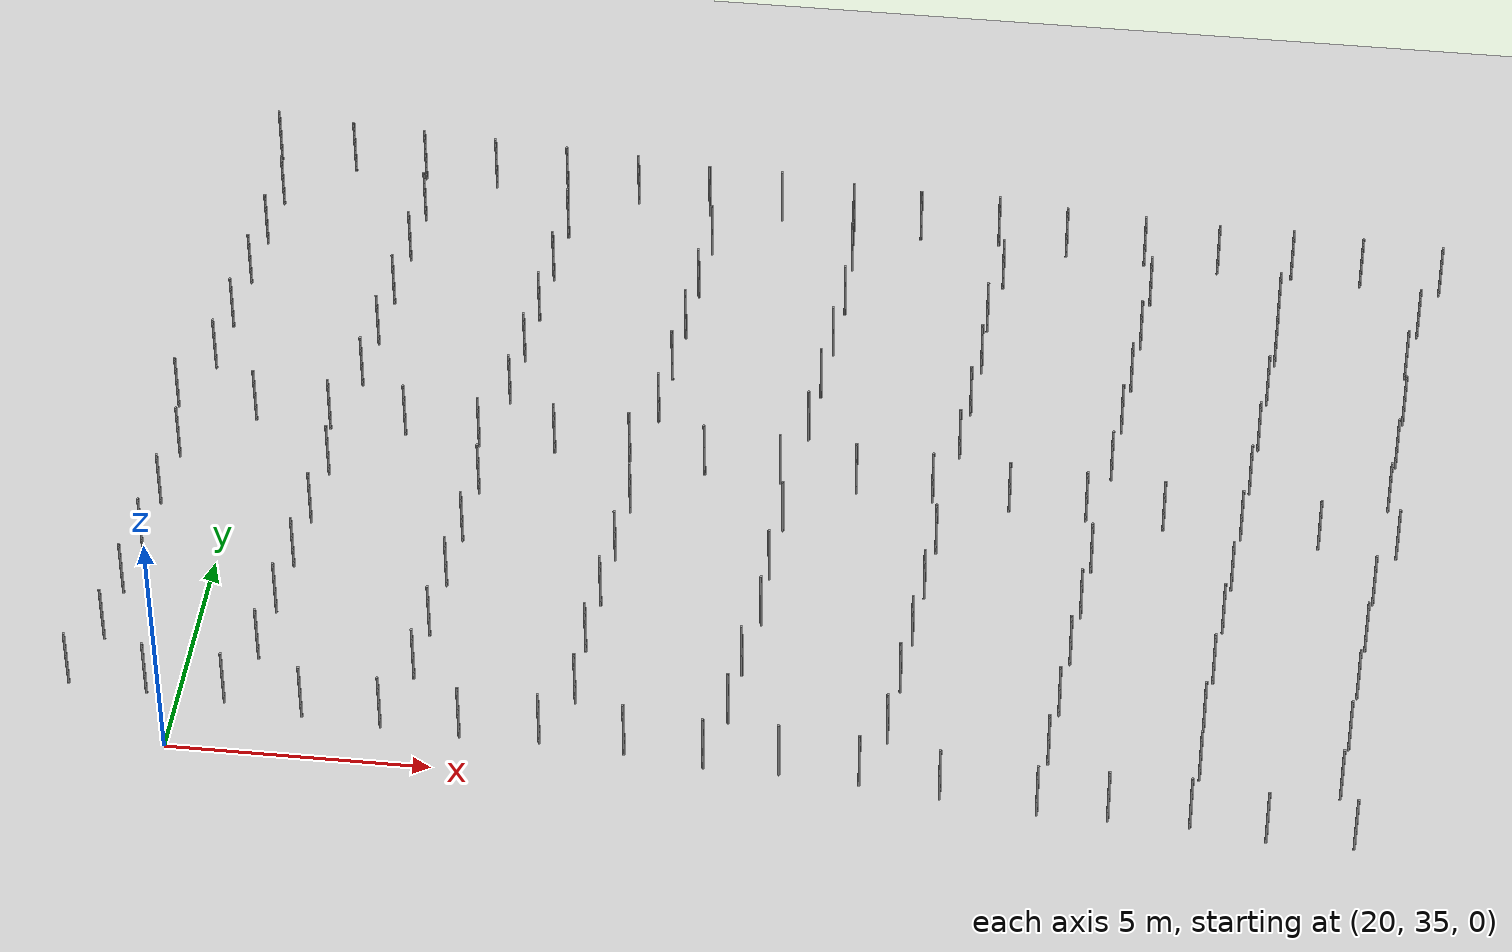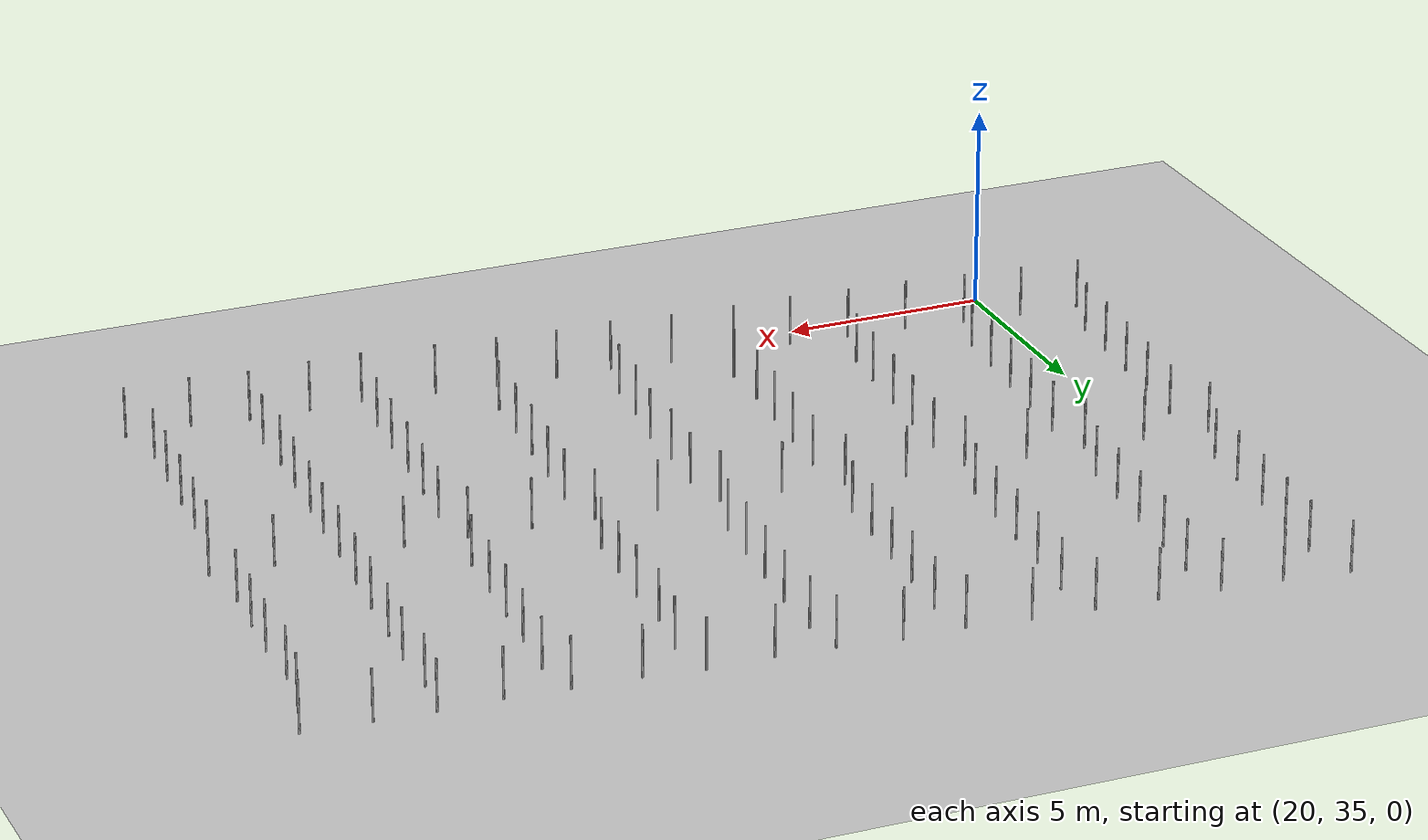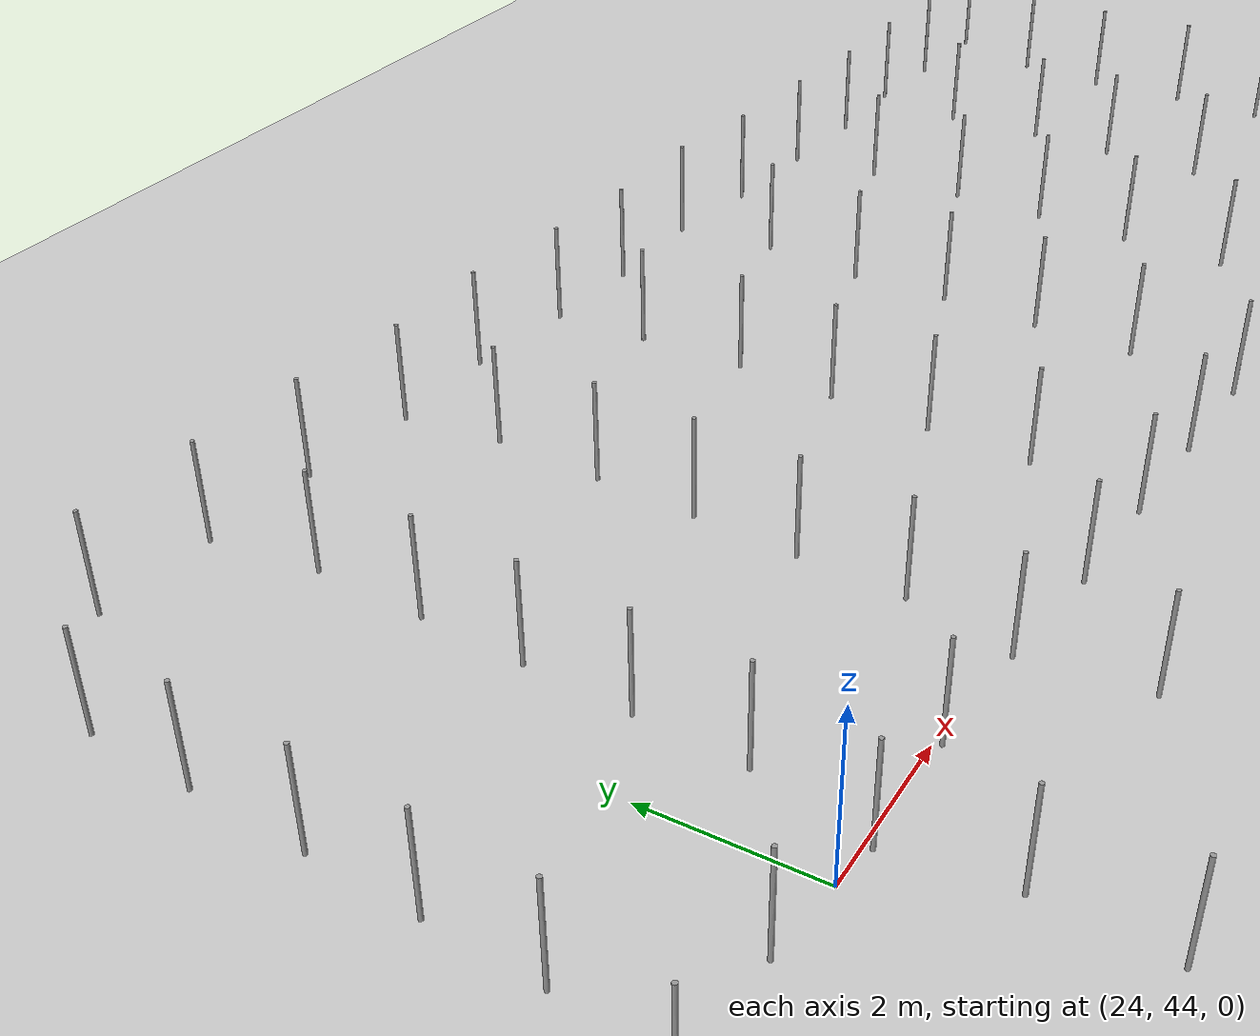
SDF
<?xml version="1.0" encoding="utf-8"?>
<sdf version="1.4">
	<world name="default">
		<model name="pole_0">
			<static>1</static>
			<pose>18.3 37.7 0.635 0.0 0.0 0.0</pose>
			<link name="link">
				<kinematic>0</kinematic>
				<inertial>
					<mass>1</mass>
					<inertia>
						<ixz>0</ixz>
						<ixx>1</ixx>
						<ixy>0</ixy>
						<izz>1</izz>
						<iyy>1</iyy>
						<iyz>0</iyz>
					</inertia>
				</inertial>
				<self_collide>0</self_collide>
				<gravity>1</gravity>
				<collision name="collision">
					<geometry>
						<cylinder>
							<length>1.27</length>
							<radius>0.025</radius>
						</cylinder>
					</geometry>
					<max_contacts>10</max_contacts>
					<surface>
						<contact>
							<ode></ode>
						</contact>
						<friction>
							<ode></ode>
						</friction>
						<bounce></bounce>
					</surface>
				</collision>
				<visual name="visual">
					<geometry>
						<cylinder>
							<length>1.27</length>
							<radius>0.025</radius>
						</cylinder>
					</geometry>
					<material>
						<script>
							<uri>file://media/materials/scripts/gazebo.material</uri>
							<name>Gazebo/Grey</name>
						</script>
					</material>
				</visual>
				<velocity_decay>
					<linear>0</linear>
					<angular>0</angular>
				</velocity_decay>
			</link>
		</model>
		<model name="pole_1">
			<static>1</static>
			<pose>21.3 37.5 0.635 0.0 0.0 0.0</pose>
			<link name="link">
				<kinematic>0</kinematic>
				<inertial>
					<mass>1</mass>
					<inertia>
						<ixz>0</ixz>
						<ixx>1</ixx>
						<ixy>0</ixy>
						<izz>1</izz>
						<iyy>1</iyy>
						<iyz>0</iyz>
					</inertia>
				</inertial>
				<self_collide>0</self_collide>
				<gravity>1</gravity>
				<collision name="collision">
					<geometry>
						<cylinder>
							<length>1.27</length>
							<radius>0.025</radius>
						</cylinder>
					</geometry>
					<max_contacts>10</max_contacts>
					<surface>
						<contact>
							<ode></ode>
						</contact>
						<friction>
							<ode></ode>
						</friction>
						<bounce></bounce>
					</surface>
				</collision>
				<visual name="visual">
					<geometry>
						<cylinder>
							<length>1.27</length>
							<radius>0.025</radius>
						</cylinder>
					</geometry>
					<material>
						<script>
							<uri>file://media/materials/scripts/gazebo.material</uri>
							<name>Gazebo/Grey</name>
						</script>
					</material>
				</visual>
				<velocity_decay>
					<linear>0</linear>
					<angular>0</angular>
				</velocity_decay>
			</link>
		</model>
		<model name="pole_2">
			<static>1</static>
			<pose>24.3 37.3 0.635 0.0 0.0 0.0</pose>
			<link name="link">
				<kinematic>0</kinematic>
				<inertial>
					<mass>1</mass>
					<inertia>
						<ixz>0</ixz>
						<ixx>1</ixx>
						<ixy>0</ixy>
						<izz>1</izz>
						<iyy>1</iyy>
						<iyz>0</iyz>
					</inertia>
				</inertial>
				<self_collide>0</self_collide>
				<gravity>1</gravity>
				<collision name="collision">
					<geometry>
						<cylinder>
							<length>1.27</length>
							<radius>0.025</radius>
						</cylinder>
					</geometry>
					<max_contacts>10</max_contacts>
					<surface>
						<contact>
							<ode></ode>
						</contact>
						<friction>
							<ode></ode>
						</friction>
						<bounce></bounce>
					</surface>
				</collision>
				<visual name="visual">
					<geometry>
						<cylinder>
							<length>1.27</length>
							<radius>0.025</radius>
						</cylinder>
					</geometry>
					<material>
						<script>
							<uri>file://media/materials/scripts/gazebo.material</uri>
							<name>Gazebo/Grey</name>
						</script>
					</material>
				</visual>
				<velocity_decay>
					<linear>0</linear>
					<angular>0</angular>
				</velocity_decay>
			</link>
		</model>
		<model name="pole_3">
			<static>1</static>
			<pose>27.4 37.0 0.635 0.0 0.0 0.0</pose>
			<link name="link">
				<kinematic>0</kinematic>
				<inertial>
					<mass>1</mass>
					<inertia>
						<ixz>0</ixz>
						<ixx>1</ixx>
						<ixy>0</ixy>
						<izz>1</izz>
						<iyy>1</iyy>
						<iyz>0</iyz>
					</inertia>
				</inertial>
				<self_collide>0</self_collide>
				<gravity>1</gravity>
				<collision name="collision">
					<geometry>
						<cylinder>
							<length>1.27</length>
							<radius>0.025</radius>
						</cylinder>
					</geometry>
					<max_contacts>10</max_contacts>
					<surface>
						<contact>
							<ode></ode>
						</contact>
						<friction>
							<ode></ode>
						</friction>
						<bounce></bounce>
					</surface>
				</collision>
				<visual name="visual">
					<geometry>
						<cylinder>
							<length>1.27</length>
							<radius>0.025</radius>
						</cylinder>
					</geometry>
					<material>
						<script>
							<uri>file://media/materials/scripts/gazebo.material</uri>
							<name>Gazebo/Grey</name>
						</script>
					</material>
				</visual>
				<velocity_decay>
					<linear>0</linear>
					<angular>0</angular>
				</velocity_decay>
			</link>
		</model>
		<model name="pole_4">
			<static>1</static>
			<pose>30.3 36.8 0.635 0.0 0.0 0.0</pose>
			<link name="link">
				<kinematic>0</kinematic>
				<inertial>
					<mass>1</mass>
					<inertia>
						<ixz>0</ixz>
						<ixx>1</ixx>
						<ixy>0</ixy>
						<izz>1</izz>
						<iyy>1</iyy>
						<iyz>0</iyz>
					</inertia>
				</inertial>
				<self_collide>0</self_collide>
				<gravity>1</gravity>
				<collision name="collision">
					<geometry>
						<cylinder>
							<length>1.27</length>
							<radius>0.025</radius>
						</cylinder>
					</geometry>
					<max_contacts>10</max_contacts>
					<surface>
						<contact>
							<ode></ode>
						</contact>
						<friction>
							<ode></ode>
						</friction>
						<bounce></bounce>
					</surface>
				</collision>
				<visual name="visual">
					<geometry>
						<cylinder>
							<length>1.27</length>
							<radius>0.025</radius>
						</cylinder>
					</geometry>
					<material>
						<script>
							<uri>file://media/materials/scripts/gazebo.material</uri>
							<name>Gazebo/Grey</name>
						</script>
					</material>
				</visual>
				<velocity_decay>
					<linear>0</linear>
					<angular>0</angular>
				</velocity_decay>
			</link>
		</model>
		<model name="pole_5">
			<static>1</static>
			<pose>33.3 36.6 0.635 0.0 0.0 0.0</pose>
			<link name="link">
				<kinematic>0</kinematic>
				<inertial>
					<mass>1</mass>
					<inertia>
						<ixz>0</ixz>
						<ixx>1</ixx>
						<ixy>0</ixy>
						<izz>1</izz>
						<iyy>1</iyy>
						<iyz>0</iyz>
					</inertia>
				</inertial>
				<self_collide>0</self_collide>
				<gravity>1</gravity>
				<collision name="collision">
					<geometry>
						<cylinder>
							<length>1.27</length>
							<radius>0.025</radius>
						</cylinder>
					</geometry>
					<max_contacts>10</max_contacts>
					<surface>
						<contact>
							<ode></ode>
						</contact>
						<friction>
							<ode></ode>
						</friction>
						<bounce></bounce>
					</surface>
				</collision>
				<visual name="visual">
					<geometry>
						<cylinder>
							<length>1.27</length>
							<radius>0.025</radius>
						</cylinder>
					</geometry>
					<material>
						<script>
							<uri>file://media/materials/scripts/gazebo.material</uri>
							<name>Gazebo/Grey</name>
						</script>
					</material>
				</visual>
				<velocity_decay>
					<linear>0</linear>
					<angular>0</angular>
				</velocity_decay>
			</link>
		</model>
		<model name="pole_6">
			<static>1</static>
			<pose>36.3 36.4 0.635 0.0 0.0 0.0</pose>
			<link name="link">
				<kinematic>0</kinematic>
				<inertial>
					<mass>1</mass>
					<inertia>
						<ixz>0</ixz>
						<ixx>1</ixx>
						<ixy>0</ixy>
						<izz>1</izz>
						<iyy>1</iyy>
						<iyz>0</iyz>
					</inertia>
				</inertial>
				<self_collide>0</self_collide>
				<gravity>1</gravity>
				<collision name="collision">
					<geometry>
						<cylinder>
							<length>1.27</length>
							<radius>0.025</radius>
						</cylinder>
					</geometry>
					<max_contacts>10</max_contacts>
					<surface>
						<contact>
							<ode></ode>
						</contact>
						<friction>
							<ode></ode>
						</friction>
						<bounce></bounce>
					</surface>
				</collision>
				<visual name="visual">
					<geometry>
						<cylinder>
							<length>1.27</length>
							<radius>0.025</radius>
						</cylinder>
					</geometry>
					<material>
						<script>
							<uri>file://media/materials/scripts/gazebo.material</uri>
							<name>Gazebo/Grey</name>
						</script>
					</material>
				</visual>
				<velocity_decay>
					<linear>0</linear>
					<angular>0</angular>
				</velocity_decay>
			</link>
		</model>
		<model name="pole_7">
			<static>1</static>
			<pose>39.1 36.3 0.635 0.0 0.0 0.0</pose>
			<link name="link">
				<kinematic>0</kinematic>
				<inertial>
					<mass>1</mass>
					<inertia>
						<ixz>0</ixz>
						<ixx>1</ixx>
						<ixy>0</ixy>
						<izz>1</izz>
						<iyy>1</iyy>
						<iyz>0</iyz>
					</inertia>
				</inertial>
				<self_collide>0</self_collide>
				<gravity>1</gravity>
				<collision name="collision">
					<geometry>
						<cylinder>
							<length>1.27</length>
							<radius>0.025</radius>
						</cylinder>
					</geometry>
					<max_contacts>10</max_contacts>
					<surface>
						<contact>
							<ode></ode>
						</contact>
						<friction>
							<ode></ode>
						</friction>
						<bounce></bounce>
					</surface>
				</collision>
				<visual name="visual">
					<geometry>
						<cylinder>
							<length>1.27</length>
							<radius>0.025</radius>
						</cylinder>
					</geometry>
					<material>
						<script>
							<uri>file://media/materials/scripts/gazebo.material</uri>
							<name>Gazebo/Grey</name>
						</script>
					</material>
				</visual>
				<velocity_decay>
					<linear>0</linear>
					<angular>0</angular>
				</velocity_decay>
			</link>
		</model>
		<model name="pole_8">
			<static>1</static>
			<pose>41.7 36.1 0.635 0.0 0.0 0.0</pose>
			<link name="link">
				<kinematic>0</kinematic>
				<inertial>
					<mass>1</mass>
					<inertia>
						<ixz>0</ixz>
						<ixx>1</ixx>
						<ixy>0</ixy>
						<izz>1</izz>
						<iyy>1</iyy>
						<iyz>0</iyz>
					</inertia>
				</inertial>
				<self_collide>0</self_collide>
				<gravity>1</gravity>
				<collision name="collision">
					<geometry>
						<cylinder>
							<length>1.27</length>
							<radius>0.025</radius>
						</cylinder>
					</geometry>
					<max_contacts>10</max_contacts>
					<surface>
						<contact>
							<ode></ode>
						</contact>
						<friction>
							<ode></ode>
						</friction>
						<bounce></bounce>
					</surface>
				</collision>
				<visual name="visual">
					<geometry>
						<cylinder>
							<length>1.27</length>
							<radius>0.025</radius>
						</cylinder>
					</geometry>
					<material>
						<script>
							<uri>file://media/materials/scripts/gazebo.material</uri>
							<name>Gazebo/Grey</name>
						</script>
					</material>
				</visual>
				<velocity_decay>
					<linear>0</linear>
					<angular>0</angular>
				</velocity_decay>
			</link>
		</model>
		<model name="pole_9">
			<static>1</static>
			<pose>18.4 39.0 0.635 0.0 0.0 0.0</pose>
			<link name="link">
				<kinematic>0</kinematic>
				<inertial>
					<mass>1</mass>
					<inertia>
						<ixz>0</ixz>
						<ixx>1</ixx>
						<ixy>0</ixy>
						<izz>1</izz>
						<iyy>1</iyy>
						<iyz>0</iyz>
					</inertia>
				</inertial>
				<self_collide>0</self_collide>
				<gravity>1</gravity>
				<collision name="collision">
					<geometry>
						<cylinder>
							<length>1.27</length>
							<radius>0.025</radius>
						</cylinder>
					</geometry>
					<max_contacts>10</max_contacts>
					<surface>
						<contact>
							<ode></ode>
						</contact>
						<friction>
							<ode></ode>
						</friction>
						<bounce></bounce>
					</surface>
				</collision>
				<visual name="visual">
					<geometry>
						<cylinder>
							<length>1.27</length>
							<radius>0.025</radius>
						</cylinder>
					</geometry>
					<material>
						<script>
							<uri>file://media/materials/scripts/gazebo.material</uri>
							<name>Gazebo/Grey</name>
						</script>
					</material>
				</visual>
				<velocity_decay>
					<linear>0</linear>
					<angular>0</angular>
				</velocity_decay>
			</link>
		</model>
		<model name="pole_10">
			<static>1</static>
			<pose>21.4 38.8 0.635 0.0 0.0 0.0</pose>
			<link name="link">
				<kinematic>0</kinematic>
				<inertial>
					<mass>1</mass>
					<inertia>
						<ixz>0</ixz>
						<ixx>1</ixx>
						<ixy>0</ixy>
						<izz>1</izz>
						<iyy>1</iyy>
						<iyz>0</iyz>
					</inertia>
				</inertial>
				<self_collide>0</self_collide>
				<gravity>1</gravity>
				<collision name="collision">
					<geometry>
						<cylinder>
							<length>1.27</length>
							<radius>0.025</radius>
						</cylinder>
					</geometry>
					<max_contacts>10</max_contacts>
					<surface>
						<contact>
							<ode></ode>
						</contact>
						<friction>
							<ode></ode>
						</friction>
						<bounce></bounce>
					</surface>
				</collision>
				<visual name="visual">
					<geometry>
						<cylinder>
							<length>1.27</length>
							<radius>0.025</radius>
						</cylinder>
					</geometry>
					<material>
						<script>
							<uri>file://media/materials/scripts/gazebo.material</uri>
							<name>Gazebo/Grey</name>
						</script>
					</material>
				</visual>
				<velocity_decay>
					<linear>0</linear>
					<angular>0</angular>
				</velocity_decay>
			</link>
		</model>
		<model name="pole_11">
			<static>1</static>
			<pose>24.4 38.5 0.635 0.0 0.0 0.0</pose>
			<link name="link">
				<kinematic>0</kinematic>
				<inertial>
					<mass>1</mass>
					<inertia>
						<ixz>0</ixz>
						<ixx>1</ixx>
						<ixy>0</ixy>
						<izz>1</izz>
						<iyy>1</iyy>
						<iyz>0</iyz>
					</inertia>
				</inertial>
				<self_collide>0</self_collide>
				<gravity>1</gravity>
				<collision name="collision">
					<geometry>
						<cylinder>
							<length>1.27</length>
							<radius>0.025</radius>
						</cylinder>
					</geometry>
					<max_contacts>10</max_contacts>
					<surface>
						<contact>
							<ode></ode>
						</contact>
						<friction>
							<ode></ode>
						</friction>
						<bounce></bounce>
					</surface>
				</collision>
				<visual name="visual">
					<geometry>
						<cylinder>
							<length>1.27</length>
							<radius>0.025</radius>
						</cylinder>
					</geometry>
					<material>
						<script>
							<uri>file://media/materials/scripts/gazebo.material</uri>
							<name>Gazebo/Grey</name>
						</script>
					</material>
				</visual>
				<velocity_decay>
					<linear>0</linear>
					<angular>0</angular>
				</velocity_decay>
			</link>
		</model>
		<model name="pole_12">
			<static>1</static>
			<pose>27.4 38.4 0.635 0.0 0.0 0.0</pose>
			<link name="link">
				<kinematic>0</kinematic>
				<inertial>
					<mass>1</mass>
					<inertia>
						<ixz>0</ixz>
						<ixx>1</ixx>
						<ixy>0</ixy>
						<izz>1</izz>
						<iyy>1</iyy>
						<iyz>0</iyz>
					</inertia>
				</inertial>
				<self_collide>0</self_collide>
				<gravity>1</gravity>
				<collision name="collision">
					<geometry>
						<cylinder>
							<length>1.27</length>
							<radius>0.025</radius>
						</cylinder>
					</geometry>
					<max_contacts>10</max_contacts>
					<surface>
						<contact>
							<ode></ode>
						</contact>
						<friction>
							<ode></ode>
						</friction>
						<bounce></bounce>
					</surface>
				</collision>
				<visual name="visual">
					<geometry>
						<cylinder>
							<length>1.27</length>
							<radius>0.025</radius>
						</cylinder>
					</geometry>
					<material>
						<script>
							<uri>file://media/materials/scripts/gazebo.material</uri>
							<name>Gazebo/Grey</name>
						</script>
					</material>
				</visual>
				<velocity_decay>
					<linear>0</linear>
					<angular>0</angular>
				</velocity_decay>
			</link>
		</model>
		<model name="pole_13">
			<static>1</static>
			<pose>30.4 38.1 0.635 0.0 0.0 0.0</pose>
			<link name="link">
				<kinematic>0</kinematic>
				<inertial>
					<mass>1</mass>
					<inertia>
						<ixz>0</ixz>
						<ixx>1</ixx>
						<ixy>0</ixy>
						<izz>1</izz>
						<iyy>1</iyy>
						<iyz>0</iyz>
					</inertia>
				</inertial>
				<self_collide>0</self_collide>
				<gravity>1</gravity>
				<collision name="collision">
					<geometry>
						<cylinder>
							<length>1.27</length>
							<radius>0.025</radius>
						</cylinder>
					</geometry>
					<max_contacts>10</max_contacts>
					<surface>
						<contact>
							<ode></ode>
						</contact>
						<friction>
							<ode></ode>
						</friction>
						<bounce></bounce>
					</surface>
				</collision>
				<visual name="visual">
					<geometry>
						<cylinder>
							<length>1.27</length>
							<radius>0.025</radius>
						</cylinder>
					</geometry>
					<material>
						<script>
							<uri>file://media/materials/scripts/gazebo.material</uri>
							<name>Gazebo/Grey</name>
						</script>
					</material>
				</visual>
				<velocity_decay>
					<linear>0</linear>
					<angular>0</angular>
				</velocity_decay>
			</link>
		</model>
		<model name="pole_14">
			<static>1</static>
			<pose>33.4 38.0 0.635 0.0 0.0 0.0</pose>
			<link name="link">
				<kinematic>0</kinematic>
				<inertial>
					<mass>1</mass>
					<inertia>
						<ixz>0</ixz>
						<ixx>1</ixx>
						<ixy>0</ixy>
						<izz>1</izz>
						<iyy>1</iyy>
						<iyz>0</iyz>
					</inertia>
				</inertial>
				<self_collide>0</self_collide>
				<gravity>1</gravity>
				<collision name="collision">
					<geometry>
						<cylinder>
							<length>1.27</length>
							<radius>0.025</radius>
						</cylinder>
					</geometry>
					<max_contacts>10</max_contacts>
					<surface>
						<contact>
							<ode></ode>
						</contact>
						<friction>
							<ode></ode>
						</friction>
						<bounce></bounce>
					</surface>
				</collision>
				<visual name="visual">
					<geometry>
						<cylinder>
							<length>1.27</length>
							<radius>0.025</radius>
						</cylinder>
					</geometry>
					<material>
						<script>
							<uri>file://media/materials/scripts/gazebo.material</uri>
							<name>Gazebo/Grey</name>
						</script>
					</material>
				</visual>
				<velocity_decay>
					<linear>0</linear>
					<angular>0</angular>
				</velocity_decay>
			</link>
		</model>
		<model name="pole_15">
			<static>1</static>
			<pose>36.4 37.7 0.635 0.0 0.0 0.0</pose>
			<link name="link">
				<kinematic>0</kinematic>
				<inertial>
					<mass>1</mass>
					<inertia>
						<ixz>0</ixz>
						<ixx>1</ixx>
						<ixy>0</ixy>
						<izz>1</izz>
						<iyy>1</iyy>
						<iyz>0</iyz>
					</inertia>
				</inertial>
				<self_collide>0</self_collide>
				<gravity>1</gravity>
				<collision name="collision">
					<geometry>
						<cylinder>
							<length>1.27</length>
							<radius>0.025</radius>
						</cylinder>
					</geometry>
					<max_contacts>10</max_contacts>
					<surface>
						<contact>
							<ode></ode>
						</contact>
						<friction>
							<ode></ode>
						</friction>
						<bounce></bounce>
					</surface>
				</collision>
				<visual name="visual">
					<geometry>
						<cylinder>
							<length>1.27</length>
							<radius>0.025</radius>
						</cylinder>
					</geometry>
					<material>
						<script>
							<uri>file://media/materials/scripts/gazebo.material</uri>
							<name>Gazebo/Grey</name>
						</script>
					</material>
				</visual>
				<velocity_decay>
					<linear>0</linear>
					<angular>0</angular>
				</velocity_decay>
			</link>
		</model>
		<model name="pole_16">
			<static>1</static>
			<pose>39.1 37.6 0.635 0.0 0.0 0.0</pose>
			<link name="link">
				<kinematic>0</kinematic>
				<inertial>
					<mass>1</mass>
					<inertia>
						<ixz>0</ixz>
						<ixx>1</ixx>
						<ixy>0</ixy>
						<izz>1</izz>
						<iyy>1</iyy>
						<iyz>0</iyz>
					</inertia>
				</inertial>
				<self_collide>0</self_collide>
				<gravity>1</gravity>
				<collision name="collision">
					<geometry>
						<cylinder>
							<length>1.27</length>
							<radius>0.025</radius>
						</cylinder>
					</geometry>
					<max_contacts>10</max_contacts>
					<surface>
						<contact>
							<ode></ode>
						</contact>
						<friction>
							<ode></ode>
						</friction>
						<bounce></bounce>
					</surface>
				</collision>
				<visual name="visual">
					<geometry>
						<cylinder>
							<length>1.27</length>
							<radius>0.025</radius>
						</cylinder>
					</geometry>
					<material>
						<script>
							<uri>file://media/materials/scripts/gazebo.material</uri>
							<name>Gazebo/Grey</name>
						</script>
					</material>
				</visual>
				<velocity_decay>
					<linear>0</linear>
					<angular>0</angular>
				</velocity_decay>
			</link>
		</model>
		<model name="pole_17">
			<static>1</static>
			<pose>41.8 37.4 0.635 0.0 0.0 0.0</pose>
			<link name="link">
				<kinematic>0</kinematic>
				<inertial>
					<mass>1</mass>
					<inertia>
						<ixz>0</ixz>
						<ixx>1</ixx>
						<ixy>0</ixy>
						<izz>1</izz>
						<iyy>1</iyy>
						<iyz>0</iyz>
					</inertia>
				</inertial>
				<self_collide>0</self_collide>
				<gravity>1</gravity>
				<collision name="collision">
					<geometry>
						<cylinder>
							<length>1.27</length>
							<radius>0.025</radius>
						</cylinder>
					</geometry>
					<max_contacts>10</max_contacts>
					<surface>
						<contact>
							<ode></ode>
						</contact>
						<friction>
							<ode></ode>
						</friction>
						<bounce></bounce>
					</surface>
				</collision>
				<visual name="visual">
					<geometry>
						<cylinder>
							<length>1.27</length>
							<radius>0.025</radius>
						</cylinder>
					</geometry>
					<material>
						<script>
							<uri>file://media/materials/scripts/gazebo.material</uri>
							<name>Gazebo/Grey</name>
						</script>
					</material>
				</visual>
				<velocity_decay>
					<linear>0</linear>
					<angular>0</angular>
				</velocity_decay>
			</link>
		</model>
		<model name="pole_18">
			<static>1</static>
			<pose>18.5 40.3 0.635 0.0 0.0 0.0</pose>
			<link name="link">
				<kinematic>0</kinematic>
				<inertial>
					<mass>1</mass>
					<inertia>
						<ixz>0</ixz>
						<ixx>1</ixx>
						<ixy>0</ixy>
						<izz>1</izz>
						<iyy>1</iyy>
						<iyz>0</iyz>
					</inertia>
				</inertial>
				<self_collide>0</self_collide>
				<gravity>1</gravity>
				<collision name="collision">
					<geometry>
						<cylinder>
							<length>1.27</length>
							<radius>0.025</radius>
						</cylinder>
					</geometry>
					<max_contacts>10</max_contacts>
					<surface>
						<contact>
							<ode></ode>
						</contact>
						<friction>
							<ode></ode>
						</friction>
						<bounce></bounce>
					</surface>
				</collision>
				<visual name="visual">
					<geometry>
						<cylinder>
							<length>1.27</length>
							<radius>0.025</radius>
						</cylinder>
					</geometry>
					<material>
						<script>
							<uri>file://media/materials/scripts/gazebo.material</uri>
							<name>Gazebo/Grey</name>
						</script>
					</material>
				</visual>
				<velocity_decay>
					<linear>0</linear>
					<angular>0</angular>
				</velocity_decay>
			</link>
		</model>
		<model name="pole_19">
			<static>1</static>
			<pose>21.5 40.1 0.635 0.0 0.0 0.0</pose>
			<link name="link">
				<kinematic>0</kinematic>
				<inertial>
					<mass>1</mass>
					<inertia>
						<ixz>0</ixz>
						<ixx>1</ixx>
						<ixy>0</ixy>
						<izz>1</izz>
						<iyy>1</iyy>
						<iyz>0</iyz>
					</inertia>
				</inertial>
				<self_collide>0</self_collide>
				<gravity>1</gravity>
				<collision name="collision">
					<geometry>
						<cylinder>
							<length>1.27</length>
							<radius>0.025</radius>
						</cylinder>
					</geometry>
					<max_contacts>10</max_contacts>
					<surface>
						<contact>
							<ode></ode>
						</contact>
						<friction>
							<ode></ode>
						</friction>
						<bounce></bounce>
					</surface>
				</collision>
				<visual name="visual">
					<geometry>
						<cylinder>
							<length>1.27</length>
							<radius>0.025</radius>
						</cylinder>
					</geometry>
					<material>
						<script>
							<uri>file://media/materials/scripts/gazebo.material</uri>
							<name>Gazebo/Grey</name>
						</script>
					</material>
				</visual>
				<velocity_decay>
					<linear>0</linear>
					<angular>0</angular>
				</velocity_decay>
			</link>
		</model>
		<model name="pole_20">
			<static>1</static>
			<pose>24.5 39.9 0.635 0.0 0.0 0.0</pose>
			<link name="link">
				<kinematic>0</kinematic>
				<inertial>
					<mass>1</mass>
					<inertia>
						<ixz>0</ixz>
						<ixx>1</ixx>
						<ixy>0</ixy>
						<izz>1</izz>
						<iyy>1</iyy>
						<iyz>0</iyz>
					</inertia>
				</inertial>
				<self_collide>0</self_collide>
				<gravity>1</gravity>
				<collision name="collision">
					<geometry>
						<cylinder>
							<length>1.27</length>
							<radius>0.025</radius>
						</cylinder>
					</geometry>
					<max_contacts>10</max_contacts>
					<surface>
						<contact>
							<ode></ode>
						</contact>
						<friction>
							<ode></ode>
						</friction>
						<bounce></bounce>
					</surface>
				</collision>
				<visual name="visual">
					<geometry>
						<cylinder>
							<length>1.27</length>
							<radius>0.025</radius>
						</cylinder>
					</geometry>
					<material>
						<script>
							<uri>file://media/materials/scripts/gazebo.material</uri>
							<name>Gazebo/Grey</name>
						</script>
					</material>
				</visual>
				<velocity_decay>
					<linear>0</linear>
					<angular>0</angular>
				</velocity_decay>
			</link>
		</model>
		<model name="pole_21">
			<static>1</static>
			<pose>27.5 39.7 0.635 0.0 0.0 0.0</pose>
			<link name="link">
				<kinematic>0</kinematic>
				<inertial>
					<mass>1</mass>
					<inertia>
						<ixz>0</ixz>
						<ixx>1</ixx>
						<ixy>0</ixy>
						<izz>1</izz>
						<iyy>1</iyy>
						<iyz>0</iyz>
					</inertia>
				</inertial>
				<self_collide>0</self_collide>
				<gravity>1</gravity>
				<collision name="collision">
					<geometry>
						<cylinder>
							<length>1.27</length>
							<radius>0.025</radius>
						</cylinder>
					</geometry>
					<max_contacts>10</max_contacts>
					<surface>
						<contact>
							<ode></ode>
						</contact>
						<friction>
							<ode></ode>
						</friction>
						<bounce></bounce>
					</surface>
				</collision>
				<visual name="visual">
					<geometry>
						<cylinder>
							<length>1.27</length>
							<radius>0.025</radius>
						</cylinder>
					</geometry>
					<material>
						<script>
							<uri>file://media/materials/scripts/gazebo.material</uri>
							<name>Gazebo/Grey</name>
						</script>
					</material>
				</visual>
				<velocity_decay>
					<linear>0</linear>
					<angular>0</angular>
				</velocity_decay>
			</link>
		</model>
		<model name="pole_22">
			<static>1</static>
			<pose>30.6 39.5 0.635 0.0 0.0 0.0</pose>
			<link name="link">
				<kinematic>0</kinematic>
				<inertial>
					<mass>1</mass>
					<inertia>
						<ixz>0</ixz>
						<ixx>1</ixx>
						<ixy>0</ixy>
						<izz>1</izz>
						<iyy>1</iyy>
						<iyz>0</iyz>
					</inertia>
				</inertial>
				<self_collide>0</self_collide>
				<gravity>1</gravity>
				<collision name="collision">
					<geometry>
						<cylinder>
							<length>1.27</length>
							<radius>0.025</radius>
						</cylinder>
					</geometry>
					<max_contacts>10</max_contacts>
					<surface>
						<contact>
							<ode></ode>
						</contact>
						<friction>
							<ode></ode>
						</friction>
						<bounce></bounce>
					</surface>
				</collision>
				<visual name="visual">
					<geometry>
						<cylinder>
							<length>1.27</length>
							<radius>0.025</radius>
						</cylinder>
					</geometry>
					<material>
						<script>
							<uri>file://media/materials/scripts/gazebo.material</uri>
							<name>Gazebo/Grey</name>
						</script>
					</material>
				</visual>
				<velocity_decay>
					<linear>0</linear>
					<angular>0</angular>
				</velocity_decay>
			</link>
		</model>
		<model name="pole_23">
			<static>1</static>
			<pose>33.5 39.3 0.635 0.0 0.0 0.0</pose>
			<link name="link">
				<kinematic>0</kinematic>
				<inertial>
					<mass>1</mass>
					<inertia>
						<ixz>0</ixz>
						<ixx>1</ixx>
						<ixy>0</ixy>
						<izz>1</izz>
						<iyy>1</iyy>
						<iyz>0</iyz>
					</inertia>
				</inertial>
				<self_collide>0</self_collide>
				<gravity>1</gravity>
				<collision name="collision">
					<geometry>
						<cylinder>
							<length>1.27</length>
							<radius>0.025</radius>
						</cylinder>
					</geometry>
					<max_contacts>10</max_contacts>
					<surface>
						<contact>
							<ode></ode>
						</contact>
						<friction>
							<ode></ode>
						</friction>
						<bounce></bounce>
					</surface>
				</collision>
				<visual name="visual">
					<geometry>
						<cylinder>
							<length>1.27</length>
							<radius>0.025</radius>
						</cylinder>
					</geometry>
					<material>
						<script>
							<uri>file://media/materials/scripts/gazebo.material</uri>
							<name>Gazebo/Grey</name>
						</script>
					</material>
				</visual>
				<velocity_decay>
					<linear>0</linear>
					<angular>0</angular>
				</velocity_decay>
			</link>
		</model>
		<model name="pole_24">
			<static>1</static>
			<pose>36.5 39.1 0.635 0.0 0.0 0.0</pose>
			<link name="link">
				<kinematic>0</kinematic>
				<inertial>
					<mass>1</mass>
					<inertia>
						<ixz>0</ixz>
						<ixx>1</ixx>
						<ixy>0</ixy>
						<izz>1</izz>
						<iyy>1</iyy>
						<iyz>0</iyz>
					</inertia>
				</inertial>
				<self_collide>0</self_collide>
				<gravity>1</gravity>
				<collision name="collision">
					<geometry>
						<cylinder>
							<length>1.27</length>
							<radius>0.025</radius>
						</cylinder>
					</geometry>
					<max_contacts>10</max_contacts>
					<surface>
						<contact>
							<ode></ode>
						</contact>
						<friction>
							<ode></ode>
						</friction>
						<bounce></bounce>
					</surface>
				</collision>
				<visual name="visual">
					<geometry>
						<cylinder>
							<length>1.27</length>
							<radius>0.025</radius>
						</cylinder>
					</geometry>
					<material>
						<script>
							<uri>file://media/materials/scripts/gazebo.material</uri>
							<name>Gazebo/Grey</name>
						</script>
					</material>
				</visual>
				<velocity_decay>
					<linear>0</linear>
					<angular>0</angular>
				</velocity_decay>
			</link>
		</model>
		<model name="pole_25">
			<static>1</static>
			<pose>39.2 38.9 0.635 0.0 0.0 0.0</pose>
			<link name="link">
				<kinematic>0</kinematic>
				<inertial>
					<mass>1</mass>
					<inertia>
						<ixz>0</ixz>
						<ixx>1</ixx>
						<ixy>0</ixy>
						<izz>1</izz>
						<iyy>1</iyy>
						<iyz>0</iyz>
					</inertia>
				</inertial>
				<self_collide>0</self_collide>
				<gravity>1</gravity>
				<collision name="collision">
					<geometry>
						<cylinder>
							<length>1.27</length>
							<radius>0.025</radius>
						</cylinder>
					</geometry>
					<max_contacts>10</max_contacts>
					<surface>
						<contact>
							<ode></ode>
						</contact>
						<friction>
							<ode></ode>
						</friction>
						<bounce></bounce>
					</surface>
				</collision>
				<visual name="visual">
					<geometry>
						<cylinder>
							<length>1.27</length>
							<radius>0.025</radius>
						</cylinder>
					</geometry>
					<material>
						<script>
							<uri>file://media/materials/scripts/gazebo.material</uri>
							<name>Gazebo/Grey</name>
						</script>
					</material>
				</visual>
				<velocity_decay>
					<linear>0</linear>
					<angular>0</angular>
				</velocity_decay>
			</link>
		</model>
		<model name="pole_26">
			<static>1</static>
			<pose>41.9 38.8 0.635 0.0 0.0 0.0</pose>
			<link name="link">
				<kinematic>0</kinematic>
				<inertial>
					<mass>1</mass>
					<inertia>
						<ixz>0</ixz>
						<ixx>1</ixx>
						<ixy>0</ixy>
						<izz>1</izz>
						<iyy>1</iyy>
						<iyz>0</iyz>
					</inertia>
				</inertial>
				<self_collide>0</self_collide>
				<gravity>1</gravity>
				<collision name="collision">
					<geometry>
						<cylinder>
							<length>1.27</length>
							<radius>0.025</radius>
						</cylinder>
					</geometry>
					<max_contacts>10</max_contacts>
					<surface>
						<contact>
							<ode></ode>
						</contact>
						<friction>
							<ode></ode>
						</friction>
						<bounce></bounce>
					</surface>
				</collision>
				<visual name="visual">
					<geometry>
						<cylinder>
							<length>1.27</length>
							<radius>0.025</radius>
						</cylinder>
					</geometry>
					<material>
						<script>
							<uri>file://media/materials/scripts/gazebo.material</uri>
							<name>Gazebo/Grey</name>
						</script>
					</material>
				</visual>
				<velocity_decay>
					<linear>0</linear>
					<angular>0</angular>
				</velocity_decay>
			</link>
		</model>
		<model name="pole_27">
			<static>1</static>
			<pose>18.6 41.6 0.635 0.0 0.0 0.0</pose>
			<link name="link">
				<kinematic>0</kinematic>
				<inertial>
					<mass>1</mass>
					<inertia>
						<ixz>0</ixz>
						<ixx>1</ixx>
						<ixy>0</ixy>
						<izz>1</izz>
						<iyy>1</iyy>
						<iyz>0</iyz>
					</inertia>
				</inertial>
				<self_collide>0</self_collide>
				<gravity>1</gravity>
				<collision name="collision">
					<geometry>
						<cylinder>
							<length>1.27</length>
							<radius>0.025</radius>
						</cylinder>
					</geometry>
					<max_contacts>10</max_contacts>
					<surface>
						<contact>
							<ode></ode>
						</contact>
						<friction>
							<ode></ode>
						</friction>
						<bounce></bounce>
					</surface>
				</collision>
				<visual name="visual">
					<geometry>
						<cylinder>
							<length>1.27</length>
							<radius>0.025</radius>
						</cylinder>
					</geometry>
					<material>
						<script>
							<uri>file://media/materials/scripts/gazebo.material</uri>
							<name>Gazebo/Grey</name>
						</script>
					</material>
				</visual>
				<velocity_decay>
					<linear>0</linear>
					<angular>0</angular>
				</velocity_decay>
			</link>
		</model>
		<model name="pole_28">
			<static>1</static>
			<pose>21.6 41.4 0.635 0.0 0.0 0.0</pose>
			<link name="link">
				<kinematic>0</kinematic>
				<inertial>
					<mass>1</mass>
					<inertia>
						<ixz>0</ixz>
						<ixx>1</ixx>
						<ixy>0</ixy>
						<izz>1</izz>
						<iyy>1</iyy>
						<iyz>0</iyz>
					</inertia>
				</inertial>
				<self_collide>0</self_collide>
				<gravity>1</gravity>
				<collision name="collision">
					<geometry>
						<cylinder>
							<length>1.27</length>
							<radius>0.025</radius>
						</cylinder>
					</geometry>
					<max_contacts>10</max_contacts>
					<surface>
						<contact>
							<ode></ode>
						</contact>
						<friction>
							<ode></ode>
						</friction>
						<bounce></bounce>
					</surface>
				</collision>
				<visual name="visual">
					<geometry>
						<cylinder>
							<length>1.27</length>
							<radius>0.025</radius>
						</cylinder>
					</geometry>
					<material>
						<script>
							<uri>file://media/materials/scripts/gazebo.material</uri>
							<name>Gazebo/Grey</name>
						</script>
					</material>
				</visual>
				<velocity_decay>
					<linear>0</linear>
					<angular>0</angular>
				</velocity_decay>
			</link>
		</model>
		<model name="pole_29">
			<static>1</static>
			<pose>24.6 41.2 0.635 0.0 0.0 0.0</pose>
			<link name="link">
				<kinematic>0</kinematic>
				<inertial>
					<mass>1</mass>
					<inertia>
						<ixz>0</ixz>
						<ixx>1</ixx>
						<ixy>0</ixy>
						<izz>1</izz>
						<iyy>1</iyy>
						<iyz>0</iyz>
					</inertia>
				</inertial>
				<self_collide>0</self_collide>
				<gravity>1</gravity>
				<collision name="collision">
					<geometry>
						<cylinder>
							<length>1.27</length>
							<radius>0.025</radius>
						</cylinder>
					</geometry>
					<max_contacts>10</max_contacts>
					<surface>
						<contact>
							<ode></ode>
						</contact>
						<friction>
							<ode></ode>
						</friction>
						<bounce></bounce>
					</surface>
				</collision>
				<visual name="visual">
					<geometry>
						<cylinder>
							<length>1.27</length>
							<radius>0.025</radius>
						</cylinder>
					</geometry>
					<material>
						<script>
							<uri>file://media/materials/scripts/gazebo.material</uri>
							<name>Gazebo/Grey</name>
						</script>
					</material>
				</visual>
				<velocity_decay>
					<linear>0</linear>
					<angular>0</angular>
				</velocity_decay>
			</link>
		</model>
		<model name="pole_30">
			<static>1</static>
			<pose>27.6 41.0 0.635 0.0 0.0 0.0</pose>
			<link name="link">
				<kinematic>0</kinematic>
				<inertial>
					<mass>1</mass>
					<inertia>
						<ixz>0</ixz>
						<ixx>1</ixx>
						<ixy>0</ixy>
						<izz>1</izz>
						<iyy>1</iyy>
						<iyz>0</iyz>
					</inertia>
				</inertial>
				<self_collide>0</self_collide>
				<gravity>1</gravity>
				<collision name="collision">
					<geometry>
						<cylinder>
							<length>1.27</length>
							<radius>0.025</radius>
						</cylinder>
					</geometry>
					<max_contacts>10</max_contacts>
					<surface>
						<contact>
							<ode></ode>
						</contact>
						<friction>
							<ode></ode>
						</friction>
						<bounce></bounce>
					</surface>
				</collision>
				<visual name="visual">
					<geometry>
						<cylinder>
							<length>1.27</length>
							<radius>0.025</radius>
						</cylinder>
					</geometry>
					<material>
						<script>
							<uri>file://media/materials/scripts/gazebo.material</uri>
							<name>Gazebo/Grey</name>
						</script>
					</material>
				</visual>
				<velocity_decay>
					<linear>0</linear>
					<angular>0</angular>
				</velocity_decay>
			</link>
		</model>
		<model name="pole_31">
			<static>1</static>
			<pose>30.6 40.8 0.635 0.0 0.0 0.0</pose>
			<link name="link">
				<kinematic>0</kinematic>
				<inertial>
					<mass>1</mass>
					<inertia>
						<ixz>0</ixz>
						<ixx>1</ixx>
						<ixy>0</ixy>
						<izz>1</izz>
						<iyy>1</iyy>
						<iyz>0</iyz>
					</inertia>
				</inertial>
				<self_collide>0</self_collide>
				<gravity>1</gravity>
				<collision name="collision">
					<geometry>
						<cylinder>
							<length>1.27</length>
							<radius>0.025</radius>
						</cylinder>
					</geometry>
					<max_contacts>10</max_contacts>
					<surface>
						<contact>
							<ode></ode>
						</contact>
						<friction>
							<ode></ode>
						</friction>
						<bounce></bounce>
					</surface>
				</collision>
				<visual name="visual">
					<geometry>
						<cylinder>
							<length>1.27</length>
							<radius>0.025</radius>
						</cylinder>
					</geometry>
					<material>
						<script>
							<uri>file://media/materials/scripts/gazebo.material</uri>
							<name>Gazebo/Grey</name>
						</script>
					</material>
				</visual>
				<velocity_decay>
					<linear>0</linear>
					<angular>0</angular>
				</velocity_decay>
			</link>
		</model>
		<model name="pole_32">
			<static>1</static>
			<pose>33.6 40.6 0.635 0.0 0.0 0.0</pose>
			<link name="link">
				<kinematic>0</kinematic>
				<inertial>
					<mass>1</mass>
					<inertia>
						<ixz>0</ixz>
						<ixx>1</ixx>
						<ixy>0</ixy>
						<izz>1</izz>
						<iyy>1</iyy>
						<iyz>0</iyz>
					</inertia>
				</inertial>
				<self_collide>0</self_collide>
				<gravity>1</gravity>
				<collision name="collision">
					<geometry>
						<cylinder>
							<length>1.27</length>
							<radius>0.025</radius>
						</cylinder>
					</geometry>
					<max_contacts>10</max_contacts>
					<surface>
						<contact>
							<ode></ode>
						</contact>
						<friction>
							<ode></ode>
						</friction>
						<bounce></bounce>
					</surface>
				</collision>
				<visual name="visual">
					<geometry>
						<cylinder>
							<length>1.27</length>
							<radius>0.025</radius>
						</cylinder>
					</geometry>
					<material>
						<script>
							<uri>file://media/materials/scripts/gazebo.material</uri>
							<name>Gazebo/Grey</name>
						</script>
					</material>
				</visual>
				<velocity_decay>
					<linear>0</linear>
					<angular>0</angular>
				</velocity_decay>
			</link>
		</model>
		<model name="pole_33">
			<static>1</static>
			<pose>36.6 40.4 0.635 0.0 0.0 0.0</pose>
			<link name="link">
				<kinematic>0</kinematic>
				<inertial>
					<mass>1</mass>
					<inertia>
						<ixz>0</ixz>
						<ixx>1</ixx>
						<ixy>0</ixy>
						<izz>1</izz>
						<iyy>1</iyy>
						<iyz>0</iyz>
					</inertia>
				</inertial>
				<self_collide>0</self_collide>
				<gravity>1</gravity>
				<collision name="collision">
					<geometry>
						<cylinder>
							<length>1.27</length>
							<radius>0.025</radius>
						</cylinder>
					</geometry>
					<max_contacts>10</max_contacts>
					<surface>
						<contact>
							<ode></ode>
						</contact>
						<friction>
							<ode></ode>
						</friction>
						<bounce></bounce>
					</surface>
				</collision>
				<visual name="visual">
					<geometry>
						<cylinder>
							<length>1.27</length>
							<radius>0.025</radius>
						</cylinder>
					</geometry>
					<material>
						<script>
							<uri>file://media/materials/scripts/gazebo.material</uri>
							<name>Gazebo/Grey</name>
						</script>
					</material>
				</visual>
				<velocity_decay>
					<linear>0</linear>
					<angular>0</angular>
				</velocity_decay>
			</link>
		</model>
		<model name="pole_34">
			<static>1</static>
			<pose>39.3 40.3 0.635 0.0 0.0 0.0</pose>
			<link name="link">
				<kinematic>0</kinematic>
				<inertial>
					<mass>1</mass>
					<inertia>
						<ixz>0</ixz>
						<ixx>1</ixx>
						<ixy>0</ixy>
						<izz>1</izz>
						<iyy>1</iyy>
						<iyz>0</iyz>
					</inertia>
				</inertial>
				<self_collide>0</self_collide>
				<gravity>1</gravity>
				<collision name="collision">
					<geometry>
						<cylinder>
							<length>1.27</length>
							<radius>0.025</radius>
						</cylinder>
					</geometry>
					<max_contacts>10</max_contacts>
					<surface>
						<contact>
							<ode></ode>
						</contact>
						<friction>
							<ode></ode>
						</friction>
						<bounce></bounce>
					</surface>
				</collision>
				<visual name="visual">
					<geometry>
						<cylinder>
							<length>1.27</length>
							<radius>0.025</radius>
						</cylinder>
					</geometry>
					<material>
						<script>
							<uri>file://media/materials/scripts/gazebo.material</uri>
							<name>Gazebo/Grey</name>
						</script>
					</material>
				</visual>
				<velocity_decay>
					<linear>0</linear>
					<angular>0</angular>
				</velocity_decay>
			</link>
		</model>
		<model name="pole_35">
			<static>1</static>
			<pose>42.0 40.1 0.635 0.0 0.0 0.0</pose>
			<link name="link">
				<kinematic>0</kinematic>
				<inertial>
					<mass>1</mass>
					<inertia>
						<ixz>0</ixz>
						<ixx>1</ixx>
						<ixy>0</ixy>
						<izz>1</izz>
						<iyy>1</iyy>
						<iyz>0</iyz>
					</inertia>
				</inertial>
				<self_collide>0</self_collide>
				<gravity>1</gravity>
				<collision name="collision">
					<geometry>
						<cylinder>
							<length>1.27</length>
							<radius>0.025</radius>
						</cylinder>
					</geometry>
					<max_contacts>10</max_contacts>
					<surface>
						<contact>
							<ode></ode>
						</contact>
						<friction>
							<ode></ode>
						</friction>
						<bounce></bounce>
					</surface>
				</collision>
				<visual name="visual">
					<geometry>
						<cylinder>
							<length>1.27</length>
							<radius>0.025</radius>
						</cylinder>
					</geometry>
					<material>
						<script>
							<uri>file://media/materials/scripts/gazebo.material</uri>
							<name>Gazebo/Grey</name>
						</script>
					</material>
				</visual>
				<velocity_decay>
					<linear>0</linear>
					<angular>0</angular>
				</velocity_decay>
			</link>
		</model>
		<model name="pole_36">
			<static>1</static>
			<pose>18.7 43.0 0.635 0.0 0.0 0.0</pose>
			<link name="link">
				<kinematic>0</kinematic>
				<inertial>
					<mass>1</mass>
					<inertia>
						<ixz>0</ixz>
						<ixx>1</ixx>
						<ixy>0</ixy>
						<izz>1</izz>
						<iyy>1</iyy>
						<iyz>0</iyz>
					</inertia>
				</inertial>
				<self_collide>0</self_collide>
				<gravity>1</gravity>
				<collision name="collision">
					<geometry>
						<cylinder>
							<length>1.27</length>
							<radius>0.025</radius>
						</cylinder>
					</geometry>
					<max_contacts>10</max_contacts>
					<surface>
						<contact>
							<ode></ode>
						</contact>
						<friction>
							<ode></ode>
						</friction>
						<bounce></bounce>
					</surface>
				</collision>
				<visual name="visual">
					<geometry>
						<cylinder>
							<length>1.27</length>
							<radius>0.025</radius>
						</cylinder>
					</geometry>
					<material>
						<script>
							<uri>file://media/materials/scripts/gazebo.material</uri>
							<name>Gazebo/Grey</name>
						</script>
					</material>
				</visual>
				<velocity_decay>
					<linear>0</linear>
					<angular>0</angular>
				</velocity_decay>
			</link>
		</model>
		<model name="pole_37">
			<static>1</static>
			<pose>21.7 42.8 0.635 0.0 0.0 0.0</pose>
			<link name="link">
				<kinematic>0</kinematic>
				<inertial>
					<mass>1</mass>
					<inertia>
						<ixz>0</ixz>
						<ixx>1</ixx>
						<ixy>0</ixy>
						<izz>1</izz>
						<iyy>1</iyy>
						<iyz>0</iyz>
					</inertia>
				</inertial>
				<self_collide>0</self_collide>
				<gravity>1</gravity>
				<collision name="collision">
					<geometry>
						<cylinder>
							<length>1.27</length>
							<radius>0.025</radius>
						</cylinder>
					</geometry>
					<max_contacts>10</max_contacts>
					<surface>
						<contact>
							<ode></ode>
						</contact>
						<friction>
							<ode></ode>
						</friction>
						<bounce></bounce>
					</surface>
				</collision>
				<visual name="visual">
					<geometry>
						<cylinder>
							<length>1.27</length>
							<radius>0.025</radius>
						</cylinder>
					</geometry>
					<material>
						<script>
							<uri>file://media/materials/scripts/gazebo.material</uri>
							<name>Gazebo/Grey</name>
						</script>
					</material>
				</visual>
				<velocity_decay>
					<linear>0</linear>
					<angular>0</angular>
				</velocity_decay>
			</link>
		</model>
		<model name="pole_38">
			<static>1</static>
			<pose>24.7 42.6 0.635 0.0 0.0 0.0</pose>
			<link name="link">
				<kinematic>0</kinematic>
				<inertial>
					<mass>1</mass>
					<inertia>
						<ixz>0</ixz>
						<ixx>1</ixx>
						<ixy>0</ixy>
						<izz>1</izz>
						<iyy>1</iyy>
						<iyz>0</iyz>
					</inertia>
				</inertial>
				<self_collide>0</self_collide>
				<gravity>1</gravity>
				<collision name="collision">
					<geometry>
						<cylinder>
							<length>1.27</length>
							<radius>0.025</radius>
						</cylinder>
					</geometry>
					<max_contacts>10</max_contacts>
					<surface>
						<contact>
							<ode></ode>
						</contact>
						<friction>
							<ode></ode>
						</friction>
						<bounce></bounce>
					</surface>
				</collision>
				<visual name="visual">
					<geometry>
						<cylinder>
							<length>1.27</length>
							<radius>0.025</radius>
						</cylinder>
					</geometry>
					<material>
						<script>
							<uri>file://media/materials/scripts/gazebo.material</uri>
							<name>Gazebo/Grey</name>
						</script>
					</material>
				</visual>
				<velocity_decay>
					<linear>0</linear>
					<angular>0</angular>
				</velocity_decay>
			</link>
		</model>
		<model name="pole_39">
			<static>1</static>
			<pose>27.7 42.4 0.635 0.0 0.0 0.0</pose>
			<link name="link">
				<kinematic>0</kinematic>
				<inertial>
					<mass>1</mass>
					<inertia>
						<ixz>0</ixz>
						<ixx>1</ixx>
						<ixy>0</ixy>
						<izz>1</izz>
						<iyy>1</iyy>
						<iyz>0</iyz>
					</inertia>
				</inertial>
				<self_collide>0</self_collide>
				<gravity>1</gravity>
				<collision name="collision">
					<geometry>
						<cylinder>
							<length>1.27</length>
							<radius>0.025</radius>
						</cylinder>
					</geometry>
					<max_contacts>10</max_contacts>
					<surface>
						<contact>
							<ode></ode>
						</contact>
						<friction>
							<ode></ode>
						</friction>
						<bounce></bounce>
					</surface>
				</collision>
				<visual name="visual">
					<geometry>
						<cylinder>
							<length>1.27</length>
							<radius>0.025</radius>
						</cylinder>
					</geometry>
					<material>
						<script>
							<uri>file://media/materials/scripts/gazebo.material</uri>
							<name>Gazebo/Grey</name>
						</script>
					</material>
				</visual>
				<velocity_decay>
					<linear>0</linear>
					<angular>0</angular>
				</velocity_decay>
			</link>
		</model>
		<model name="pole_40">
			<static>1</static>
			<pose>30.7 42.2 0.635 0.0 0.0 0.0</pose>
			<link name="link">
				<kinematic>0</kinematic>
				<inertial>
					<mass>1</mass>
					<inertia>
						<ixz>0</ixz>
						<ixx>1</ixx>
						<ixy>0</ixy>
						<izz>1</izz>
						<iyy>1</iyy>
						<iyz>0</iyz>
					</inertia>
				</inertial>
				<self_collide>0</self_collide>
				<gravity>1</gravity>
				<collision name="collision">
					<geometry>
						<cylinder>
							<length>1.27</length>
							<radius>0.025</radius>
						</cylinder>
					</geometry>
					<max_contacts>10</max_contacts>
					<surface>
						<contact>
							<ode></ode>
						</contact>
						<friction>
							<ode></ode>
						</friction>
						<bounce></bounce>
					</surface>
				</collision>
				<visual name="visual">
					<geometry>
						<cylinder>
							<length>1.27</length>
							<radius>0.025</radius>
						</cylinder>
					</geometry>
					<material>
						<script>
							<uri>file://media/materials/scripts/gazebo.material</uri>
							<name>Gazebo/Grey</name>
						</script>
					</material>
				</visual>
				<velocity_decay>
					<linear>0</linear>
					<angular>0</angular>
				</velocity_decay>
			</link>
		</model>
		<model name="pole_41">
			<static>1</static>
			<pose>33.7 41.9 0.635 0.0 0.0 0.0</pose>
			<link name="link">
				<kinematic>0</kinematic>
				<inertial>
					<mass>1</mass>
					<inertia>
						<ixz>0</ixz>
						<ixx>1</ixx>
						<ixy>0</ixy>
						<izz>1</izz>
						<iyy>1</iyy>
						<iyz>0</iyz>
					</inertia>
				</inertial>
				<self_collide>0</self_collide>
				<gravity>1</gravity>
				<collision name="collision">
					<geometry>
						<cylinder>
							<length>1.27</length>
							<radius>0.025</radius>
						</cylinder>
					</geometry>
					<max_contacts>10</max_contacts>
					<surface>
						<contact>
							<ode></ode>
						</contact>
						<friction>
							<ode></ode>
						</friction>
						<bounce></bounce>
					</surface>
				</collision>
				<visual name="visual">
					<geometry>
						<cylinder>
							<length>1.27</length>
							<radius>0.025</radius>
						</cylinder>
					</geometry>
					<material>
						<script>
							<uri>file://media/materials/scripts/gazebo.material</uri>
							<name>Gazebo/Grey</name>
						</script>
					</material>
				</visual>
				<velocity_decay>
					<linear>0</linear>
					<angular>0</angular>
				</velocity_decay>
			</link>
		</model>
		<model name="pole_42">
			<static>1</static>
			<pose>36.7 41.7 0.635 0.0 0.0 0.0</pose>
			<link name="link">
				<kinematic>0</kinematic>
				<inertial>
					<mass>1</mass>
					<inertia>
						<ixz>0</ixz>
						<ixx>1</ixx>
						<ixy>0</ixy>
						<izz>1</izz>
						<iyy>1</iyy>
						<iyz>0</iyz>
					</inertia>
				</inertial>
				<self_collide>0</self_collide>
				<gravity>1</gravity>
				<collision name="collision">
					<geometry>
						<cylinder>
							<length>1.27</length>
							<radius>0.025</radius>
						</cylinder>
					</geometry>
					<max_contacts>10</max_contacts>
					<surface>
						<contact>
							<ode></ode>
						</contact>
						<friction>
							<ode></ode>
						</friction>
						<bounce></bounce>
					</surface>
				</collision>
				<visual name="visual">
					<geometry>
						<cylinder>
							<length>1.27</length>
							<radius>0.025</radius>
						</cylinder>
					</geometry>
					<material>
						<script>
							<uri>file://media/materials/scripts/gazebo.material</uri>
							<name>Gazebo/Grey</name>
						</script>
					</material>
				</visual>
				<velocity_decay>
					<linear>0</linear>
					<angular>0</angular>
				</velocity_decay>
			</link>
		</model>
		<model name="pole_43">
			<static>1</static>
			<pose>39.4 41.5 0.635 0.0 0.0 0.0</pose>
			<link name="link">
				<kinematic>0</kinematic>
				<inertial>
					<mass>1</mass>
					<inertia>
						<ixz>0</ixz>
						<ixx>1</ixx>
						<ixy>0</ixy>
						<izz>1</izz>
						<iyy>1</iyy>
						<iyz>0</iyz>
					</inertia>
				</inertial>
				<self_collide>0</self_collide>
				<gravity>1</gravity>
				<collision name="collision">
					<geometry>
						<cylinder>
							<length>1.27</length>
							<radius>0.025</radius>
						</cylinder>
					</geometry>
					<max_contacts>10</max_contacts>
					<surface>
						<contact>
							<ode></ode>
						</contact>
						<friction>
							<ode></ode>
						</friction>
						<bounce></bounce>
					</surface>
				</collision>
				<visual name="visual">
					<geometry>
						<cylinder>
							<length>1.27</length>
							<radius>0.025</radius>
						</cylinder>
					</geometry>
					<material>
						<script>
							<uri>file://media/materials/scripts/gazebo.material</uri>
							<name>Gazebo/Grey</name>
						</script>
					</material>
				</visual>
				<velocity_decay>
					<linear>0</linear>
					<angular>0</angular>
				</velocity_decay>
			</link>
		</model>
		<model name="pole_44">
			<static>1</static>
			<pose>42.1 41.4 0.635 0.0 0.0 0.0</pose>
			<link name="link">
				<kinematic>0</kinematic>
				<inertial>
					<mass>1</mass>
					<inertia>
						<ixz>0</ixz>
						<ixx>1</ixx>
						<ixy>0</ixy>
						<izz>1</izz>
						<iyy>1</iyy>
						<iyz>0</iyz>
					</inertia>
				</inertial>
				<self_collide>0</self_collide>
				<gravity>1</gravity>
				<collision name="collision">
					<geometry>
						<cylinder>
							<length>1.27</length>
							<radius>0.025</radius>
						</cylinder>
					</geometry>
					<max_contacts>10</max_contacts>
					<surface>
						<contact>
							<ode></ode>
						</contact>
						<friction>
							<ode></ode>
						</friction>
						<bounce></bounce>
					</surface>
				</collision>
				<visual name="visual">
					<geometry>
						<cylinder>
							<length>1.27</length>
							<radius>0.025</radius>
						</cylinder>
					</geometry>
					<material>
						<script>
							<uri>file://media/materials/scripts/gazebo.material</uri>
							<name>Gazebo/Grey</name>
						</script>
					</material>
				</visual>
				<velocity_decay>
					<linear>0</linear>
					<angular>0</angular>
				</velocity_decay>
			</link>
		</model>
		<model name="pole_45">
			<static>1</static>
			<pose>18.9 45.7 0.635 0.0 0.0 0.0</pose>
			<link name="link">
				<kinematic>0</kinematic>
				<inertial>
					<mass>1</mass>
					<inertia>
						<ixz>0</ixz>
						<ixx>1</ixx>
						<ixy>0</ixy>
						<izz>1</izz>
						<iyy>1</iyy>
						<iyz>0</iyz>
					</inertia>
				</inertial>
				<self_collide>0</self_collide>
				<gravity>1</gravity>
				<collision name="collision">
					<geometry>
						<cylinder>
							<length>1.27</length>
							<radius>0.025</radius>
						</cylinder>
					</geometry>
					<max_contacts>10</max_contacts>
					<surface>
						<contact>
							<ode></ode>
						</contact>
						<friction>
							<ode></ode>
						</friction>
						<bounce></bounce>
					</surface>
				</collision>
				<visual name="visual">
					<geometry>
						<cylinder>
							<length>1.27</length>
							<radius>0.025</radius>
						</cylinder>
					</geometry>
					<material>
						<script>
							<uri>file://media/materials/scripts/gazebo.material</uri>
							<name>Gazebo/Grey</name>
						</script>
					</material>
				</visual>
				<velocity_decay>
					<linear>0</linear>
					<angular>0</angular>
				</velocity_decay>
			</link>
		</model>
		<model name="pole_46">
			<static>1</static>
			<pose>21.9 45.5 0.635 0.0 0.0 0.0</pose>
			<link name="link">
				<kinematic>0</kinematic>
				<inertial>
					<mass>1</mass>
					<inertia>
						<ixz>0</ixz>
						<ixx>1</ixx>
						<ixy>0</ixy>
						<izz>1</izz>
						<iyy>1</iyy>
						<iyz>0</iyz>
					</inertia>
				</inertial>
				<self_collide>0</self_collide>
				<gravity>1</gravity>
				<collision name="collision">
					<geometry>
						<cylinder>
							<length>1.27</length>
							<radius>0.025</radius>
						</cylinder>
					</geometry>
					<max_contacts>10</max_contacts>
					<surface>
						<contact>
							<ode></ode>
						</contact>
						<friction>
							<ode></ode>
						</friction>
						<bounce></bounce>
					</surface>
				</collision>
				<visual name="visual">
					<geometry>
						<cylinder>
							<length>1.27</length>
							<radius>0.025</radius>
						</cylinder>
					</geometry>
					<material>
						<script>
							<uri>file://media/materials/scripts/gazebo.material</uri>
							<name>Gazebo/Grey</name>
						</script>
					</material>
				</visual>
				<velocity_decay>
					<linear>0</linear>
					<angular>0</angular>
				</velocity_decay>
			</link>
		</model>
		<model name="pole_47">
			<static>1</static>
			<pose>24.9 45.3 0.635 0.0 0.0 0.0</pose>
			<link name="link">
				<kinematic>0</kinematic>
				<inertial>
					<mass>1</mass>
					<inertia>
						<ixz>0</ixz>
						<ixx>1</ixx>
						<ixy>0</ixy>
						<izz>1</izz>
						<iyy>1</iyy>
						<iyz>0</iyz>
					</inertia>
				</inertial>
				<self_collide>0</self_collide>
				<gravity>1</gravity>
				<collision name="collision">
					<geometry>
						<cylinder>
							<length>1.27</length>
							<radius>0.025</radius>
						</cylinder>
					</geometry>
					<max_contacts>10</max_contacts>
					<surface>
						<contact>
							<ode></ode>
						</contact>
						<friction>
							<ode></ode>
						</friction>
						<bounce></bounce>
					</surface>
				</collision>
				<visual name="visual">
					<geometry>
						<cylinder>
							<length>1.27</length>
							<radius>0.025</radius>
						</cylinder>
					</geometry>
					<material>
						<script>
							<uri>file://media/materials/scripts/gazebo.material</uri>
							<name>Gazebo/Grey</name>
						</script>
					</material>
				</visual>
				<velocity_decay>
					<linear>0</linear>
					<angular>0</angular>
				</velocity_decay>
			</link>
		</model>
		<model name="pole_48">
			<static>1</static>
			<pose>27.9 45.1 0.635 0.0 0.0 0.0</pose>
			<link name="link">
				<kinematic>0</kinematic>
				<inertial>
					<mass>1</mass>
					<inertia>
						<ixz>0</ixz>
						<ixx>1</ixx>
						<ixy>0</ixy>
						<izz>1</izz>
						<iyy>1</iyy>
						<iyz>0</iyz>
					</inertia>
				</inertial>
				<self_collide>0</self_collide>
				<gravity>1</gravity>
				<collision name="collision">
					<geometry>
						<cylinder>
							<length>1.27</length>
							<radius>0.025</radius>
						</cylinder>
					</geometry>
					<max_contacts>10</max_contacts>
					<surface>
						<contact>
							<ode></ode>
						</contact>
						<friction>
							<ode></ode>
						</friction>
						<bounce></bounce>
					</surface>
				</collision>
				<visual name="visual">
					<geometry>
						<cylinder>
							<length>1.27</length>
							<radius>0.025</radius>
						</cylinder>
					</geometry>
					<material>
						<script>
							<uri>file://media/materials/scripts/gazebo.material</uri>
							<name>Gazebo/Grey</name>
						</script>
					</material>
				</visual>
				<velocity_decay>
					<linear>0</linear>
					<angular>0</angular>
				</velocity_decay>
			</link>
		</model>
		<model name="pole_49">
			<static>1</static>
			<pose>30.9 44.9 0.635 0.0 0.0 0.0</pose>
			<link name="link">
				<kinematic>0</kinematic>
				<inertial>
					<mass>1</mass>
					<inertia>
						<ixz>0</ixz>
						<ixx>1</ixx>
						<ixy>0</ixy>
						<izz>1</izz>
						<iyy>1</iyy>
						<iyz>0</iyz>
					</inertia>
				</inertial>
				<self_collide>0</self_collide>
				<gravity>1</gravity>
				<collision name="collision">
					<geometry>
						<cylinder>
							<length>1.27</length>
							<radius>0.025</radius>
						</cylinder>
					</geometry>
					<max_contacts>10</max_contacts>
					<surface>
						<contact>
							<ode></ode>
						</contact>
						<friction>
							<ode></ode>
						</friction>
						<bounce></bounce>
					</surface>
				</collision>
				<visual name="visual">
					<geometry>
						<cylinder>
							<length>1.27</length>
							<radius>0.025</radius>
						</cylinder>
					</geometry>
					<material>
						<script>
							<uri>file://media/materials/scripts/gazebo.material</uri>
							<name>Gazebo/Grey</name>
						</script>
					</material>
				</visual>
				<velocity_decay>
					<linear>0</linear>
					<angular>0</angular>
				</velocity_decay>
			</link>
		</model>
		<model name="pole_50">
			<static>1</static>
			<pose>33.9 44.7 0.635 0.0 0.0 0.0</pose>
			<link name="link">
				<kinematic>0</kinematic>
				<inertial>
					<mass>1</mass>
					<inertia>
						<ixz>0</ixz>
						<ixx>1</ixx>
						<ixy>0</ixy>
						<izz>1</izz>
						<iyy>1</iyy>
						<iyz>0</iyz>
					</inertia>
				</inertial>
				<self_collide>0</self_collide>
				<gravity>1</gravity>
				<collision name="collision">
					<geometry>
						<cylinder>
							<length>1.27</length>
							<radius>0.025</radius>
						</cylinder>
					</geometry>
					<max_contacts>10</max_contacts>
					<surface>
						<contact>
							<ode></ode>
						</contact>
						<friction>
							<ode></ode>
						</friction>
						<bounce></bounce>
					</surface>
				</collision>
				<visual name="visual">
					<geometry>
						<cylinder>
							<length>1.27</length>
							<radius>0.025</radius>
						</cylinder>
					</geometry>
					<material>
						<script>
							<uri>file://media/materials/scripts/gazebo.material</uri>
							<name>Gazebo/Grey</name>
						</script>
					</material>
				</visual>
				<velocity_decay>
					<linear>0</linear>
					<angular>0</angular>
				</velocity_decay>
			</link>
		</model>
		<model name="pole_51">
			<static>1</static>
			<pose>36.9 44.4 0.635 0.0 0.0 0.0</pose>
			<link name="link">
				<kinematic>0</kinematic>
				<inertial>
					<mass>1</mass>
					<inertia>
						<ixz>0</ixz>
						<ixx>1</ixx>
						<ixy>0</ixy>
						<izz>1</izz>
						<iyy>1</iyy>
						<iyz>0</iyz>
					</inertia>
				</inertial>
				<self_collide>0</self_collide>
				<gravity>1</gravity>
				<collision name="collision">
					<geometry>
						<cylinder>
							<length>1.27</length>
							<radius>0.025</radius>
						</cylinder>
					</geometry>
					<max_contacts>10</max_contacts>
					<surface>
						<contact>
							<ode></ode>
						</contact>
						<friction>
							<ode></ode>
						</friction>
						<bounce></bounce>
					</surface>
				</collision>
				<visual name="visual">
					<geometry>
						<cylinder>
							<length>1.27</length>
							<radius>0.025</radius>
						</cylinder>
					</geometry>
					<material>
						<script>
							<uri>file://media/materials/scripts/gazebo.material</uri>
							<name>Gazebo/Grey</name>
						</script>
					</material>
				</visual>
				<velocity_decay>
					<linear>0</linear>
					<angular>0</angular>
				</velocity_decay>
			</link>
		</model>
		<model name="pole_52">
			<static>1</static>
			<pose>39.6 44.3 0.635 0.0 0.0 0.0</pose>
			<link name="link">
				<kinematic>0</kinematic>
				<inertial>
					<mass>1</mass>
					<inertia>
						<ixz>0</ixz>
						<ixx>1</ixx>
						<ixy>0</ixy>
						<izz>1</izz>
						<iyy>1</iyy>
						<iyz>0</iyz>
					</inertia>
				</inertial>
				<self_collide>0</self_collide>
				<gravity>1</gravity>
				<collision name="collision">
					<geometry>
						<cylinder>
							<length>1.27</length>
							<radius>0.025</radius>
						</cylinder>
					</geometry>
					<max_contacts>10</max_contacts>
					<surface>
						<contact>
							<ode></ode>
						</contact>
						<friction>
							<ode></ode>
						</friction>
						<bounce></bounce>
					</surface>
				</collision>
				<visual name="visual">
					<geometry>
						<cylinder>
							<length>1.27</length>
							<radius>0.025</radius>
						</cylinder>
					</geometry>
					<material>
						<script>
							<uri>file://media/materials/scripts/gazebo.material</uri>
							<name>Gazebo/Grey</name>
						</script>
					</material>
				</visual>
				<velocity_decay>
					<linear>0</linear>
					<angular>0</angular>
				</velocity_decay>
			</link>
		</model>
		<model name="pole_53">
			<static>1</static>
			<pose>42.3 44.1 0.635 0.0 0.0 0.0</pose>
			<link name="link">
				<kinematic>0</kinematic>
				<inertial>
					<mass>1</mass>
					<inertia>
						<ixz>0</ixz>
						<ixx>1</ixx>
						<ixy>0</ixy>
						<izz>1</izz>
						<iyy>1</iyy>
						<iyz>0</iyz>
					</inertia>
				</inertial>
				<self_collide>0</self_collide>
				<gravity>1</gravity>
				<collision name="collision">
					<geometry>
						<cylinder>
							<length>1.27</length>
							<radius>0.025</radius>
						</cylinder>
					</geometry>
					<max_contacts>10</max_contacts>
					<surface>
						<contact>
							<ode></ode>
						</contact>
						<friction>
							<ode></ode>
						</friction>
						<bounce></bounce>
					</surface>
				</collision>
				<visual name="visual">
					<geometry>
						<cylinder>
							<length>1.27</length>
							<radius>0.025</radius>
						</cylinder>
					</geometry>
					<material>
						<script>
							<uri>file://media/materials/scripts/gazebo.material</uri>
							<name>Gazebo/Grey</name>
						</script>
					</material>
				</visual>
				<velocity_decay>
					<linear>0</linear>
					<angular>0</angular>
				</velocity_decay>
			</link>
		</model>
		<model name="pole_54">
			<static>1</static>
			<pose>19.0 47.0 0.635 0.0 0.0 0.0</pose>
			<link name="link">
				<kinematic>0</kinematic>
				<inertial>
					<mass>1</mass>
					<inertia>
						<ixz>0</ixz>
						<ixx>1</ixx>
						<ixy>0</ixy>
						<izz>1</izz>
						<iyy>1</iyy>
						<iyz>0</iyz>
					</inertia>
				</inertial>
				<self_collide>0</self_collide>
				<gravity>1</gravity>
				<collision name="collision">
					<geometry>
						<cylinder>
							<length>1.27</length>
							<radius>0.025</radius>
						</cylinder>
					</geometry>
					<max_contacts>10</max_contacts>
					<surface>
						<contact>
							<ode></ode>
						</contact>
						<friction>
							<ode></ode>
						</friction>
						<bounce></bounce>
					</surface>
				</collision>
				<visual name="visual">
					<geometry>
						<cylinder>
							<length>1.27</length>
							<radius>0.025</radius>
						</cylinder>
					</geometry>
					<material>
						<script>
							<uri>file://media/materials/scripts/gazebo.material</uri>
							<name>Gazebo/Grey</name>
						</script>
					</material>
				</visual>
				<velocity_decay>
					<linear>0</linear>
					<angular>0</angular>
				</velocity_decay>
			</link>
		</model>
		<model name="pole_55">
			<static>1</static>
			<pose>22.0 46.8 0.635 0.0 0.0 0.0</pose>
			<link name="link">
				<kinematic>0</kinematic>
				<inertial>
					<mass>1</mass>
					<inertia>
						<ixz>0</ixz>
						<ixx>1</ixx>
						<ixy>0</ixy>
						<izz>1</izz>
						<iyy>1</iyy>
						<iyz>0</iyz>
					</inertia>
				</inertial>
				<self_collide>0</self_collide>
				<gravity>1</gravity>
				<collision name="collision">
					<geometry>
						<cylinder>
							<length>1.27</length>
							<radius>0.025</radius>
						</cylinder>
					</geometry>
					<max_contacts>10</max_contacts>
					<surface>
						<contact>
							<ode></ode>
						</contact>
						<friction>
							<ode></ode>
						</friction>
						<bounce></bounce>
					</surface>
				</collision>
				<visual name="visual">
					<geometry>
						<cylinder>
							<length>1.27</length>
							<radius>0.025</radius>
						</cylinder>
					</geometry>
					<material>
						<script>
							<uri>file://media/materials/scripts/gazebo.material</uri>
							<name>Gazebo/Grey</name>
						</script>
					</material>
				</visual>
				<velocity_decay>
					<linear>0</linear>
					<angular>0</angular>
				</velocity_decay>
			</link>
		</model>
		<model name="pole_56">
			<static>1</static>
			<pose>25.0 46.6 0.635 0.0 0.0 0.0</pose>
			<link name="link">
				<kinematic>0</kinematic>
				<inertial>
					<mass>1</mass>
					<inertia>
						<ixz>0</ixz>
						<ixx>1</ixx>
						<ixy>0</ixy>
						<izz>1</izz>
						<iyy>1</iyy>
						<iyz>0</iyz>
					</inertia>
				</inertial>
				<self_collide>0</self_collide>
				<gravity>1</gravity>
				<collision name="collision">
					<geometry>
						<cylinder>
							<length>1.27</length>
							<radius>0.025</radius>
						</cylinder>
					</geometry>
					<max_contacts>10</max_contacts>
					<surface>
						<contact>
							<ode></ode>
						</contact>
						<friction>
							<ode></ode>
						</friction>
						<bounce></bounce>
					</surface>
				</collision>
				<visual name="visual">
					<geometry>
						<cylinder>
							<length>1.27</length>
							<radius>0.025</radius>
						</cylinder>
					</geometry>
					<material>
						<script>
							<uri>file://media/materials/scripts/gazebo.material</uri>
							<name>Gazebo/Grey</name>
						</script>
					</material>
				</visual>
				<velocity_decay>
					<linear>0</linear>
					<angular>0</angular>
				</velocity_decay>
			</link>
		</model>
		<model name="pole_57">
			<static>1</static>
			<pose>28.0 46.4 0.635 0.0 0.0 0.0</pose>
			<link name="link">
				<kinematic>0</kinematic>
				<inertial>
					<mass>1</mass>
					<inertia>
						<ixz>0</ixz>
						<ixx>1</ixx>
						<ixy>0</ixy>
						<izz>1</izz>
						<iyy>1</iyy>
						<iyz>0</iyz>
					</inertia>
				</inertial>
				<self_collide>0</self_collide>
				<gravity>1</gravity>
				<collision name="collision">
					<geometry>
						<cylinder>
							<length>1.27</length>
							<radius>0.025</radius>
						</cylinder>
					</geometry>
					<max_contacts>10</max_contacts>
					<surface>
						<contact>
							<ode></ode>
						</contact>
						<friction>
							<ode></ode>
						</friction>
						<bounce></bounce>
					</surface>
				</collision>
				<visual name="visual">
					<geometry>
						<cylinder>
							<length>1.27</length>
							<radius>0.025</radius>
						</cylinder>
					</geometry>
					<material>
						<script>
							<uri>file://media/materials/scripts/gazebo.material</uri>
							<name>Gazebo/Grey</name>
						</script>
					</material>
				</visual>
				<velocity_decay>
					<linear>0</linear>
					<angular>0</angular>
				</velocity_decay>
			</link>
		</model>
		<model name="pole_58">
			<static>1</static>
			<pose>31.0 46.2 0.635 0.0 0.0 0.0</pose>
			<link name="link">
				<kinematic>0</kinematic>
				<inertial>
					<mass>1</mass>
					<inertia>
						<ixz>0</ixz>
						<ixx>1</ixx>
						<ixy>0</ixy>
						<izz>1</izz>
						<iyy>1</iyy>
						<iyz>0</iyz>
					</inertia>
				</inertial>
				<self_collide>0</self_collide>
				<gravity>1</gravity>
				<collision name="collision">
					<geometry>
						<cylinder>
							<length>1.27</length>
							<radius>0.025</radius>
						</cylinder>
					</geometry>
					<max_contacts>10</max_contacts>
					<surface>
						<contact>
							<ode></ode>
						</contact>
						<friction>
							<ode></ode>
						</friction>
						<bounce></bounce>
					</surface>
				</collision>
				<visual name="visual">
					<geometry>
						<cylinder>
							<length>1.27</length>
							<radius>0.025</radius>
						</cylinder>
					</geometry>
					<material>
						<script>
							<uri>file://media/materials/scripts/gazebo.material</uri>
							<name>Gazebo/Grey</name>
						</script>
					</material>
				</visual>
				<velocity_decay>
					<linear>0</linear>
					<angular>0</angular>
				</velocity_decay>
			</link>
		</model>
		<model name="pole_59">
			<static>1</static>
			<pose>34.0 46.0 0.635 0.0 0.0 0.0</pose>
			<link name="link">
				<kinematic>0</kinematic>
				<inertial>
					<mass>1</mass>
					<inertia>
						<ixz>0</ixz>
						<ixx>1</ixx>
						<ixy>0</ixy>
						<izz>1</izz>
						<iyy>1</iyy>
						<iyz>0</iyz>
					</inertia>
				</inertial>
				<self_collide>0</self_collide>
				<gravity>1</gravity>
				<collision name="collision">
					<geometry>
						<cylinder>
							<length>1.27</length>
							<radius>0.025</radius>
						</cylinder>
					</geometry>
					<max_contacts>10</max_contacts>
					<surface>
						<contact>
							<ode></ode>
						</contact>
						<friction>
							<ode></ode>
						</friction>
						<bounce></bounce>
					</surface>
				</collision>
				<visual name="visual">
					<geometry>
						<cylinder>
							<length>1.27</length>
							<radius>0.025</radius>
						</cylinder>
					</geometry>
					<material>
						<script>
							<uri>file://media/materials/scripts/gazebo.material</uri>
							<name>Gazebo/Grey</name>
						</script>
					</material>
				</visual>
				<velocity_decay>
					<linear>0</linear>
					<angular>0</angular>
				</velocity_decay>
			</link>
		</model>
		<model name="pole_60">
			<static>1</static>
			<pose>37.0 45.8 0.635 0.0 0.0 0.0</pose>
			<link name="link">
				<kinematic>0</kinematic>
				<inertial>
					<mass>1</mass>
					<inertia>
						<ixz>0</ixz>
						<ixx>1</ixx>
						<ixy>0</ixy>
						<izz>1</izz>
						<iyy>1</iyy>
						<iyz>0</iyz>
					</inertia>
				</inertial>
				<self_collide>0</self_collide>
				<gravity>1</gravity>
				<collision name="collision">
					<geometry>
						<cylinder>
							<length>1.27</length>
							<radius>0.025</radius>
						</cylinder>
					</geometry>
					<max_contacts>10</max_contacts>
					<surface>
						<contact>
							<ode></ode>
						</contact>
						<friction>
							<ode></ode>
						</friction>
						<bounce></bounce>
					</surface>
				</collision>
				<visual name="visual">
					<geometry>
						<cylinder>
							<length>1.27</length>
							<radius>0.025</radius>
						</cylinder>
					</geometry>
					<material>
						<script>
							<uri>file://media/materials/scripts/gazebo.material</uri>
							<name>Gazebo/Grey</name>
						</script>
					</material>
				</visual>
				<velocity_decay>
					<linear>0</linear>
					<angular>0</angular>
				</velocity_decay>
			</link>
		</model>
		<model name="pole_61">
			<static>1</static>
			<pose>39.7 45.6 0.635 0.0 0.0 0.0</pose>
			<link name="link">
				<kinematic>0</kinematic>
				<inertial>
					<mass>1</mass>
					<inertia>
						<ixz>0</ixz>
						<ixx>1</ixx>
						<ixy>0</ixy>
						<izz>1</izz>
						<iyy>1</iyy>
						<iyz>0</iyz>
					</inertia>
				</inertial>
				<self_collide>0</self_collide>
				<gravity>1</gravity>
				<collision name="collision">
					<geometry>
						<cylinder>
							<length>1.27</length>
							<radius>0.025</radius>
						</cylinder>
					</geometry>
					<max_contacts>10</max_contacts>
					<surface>
						<contact>
							<ode></ode>
						</contact>
						<friction>
							<ode></ode>
						</friction>
						<bounce></bounce>
					</surface>
				</collision>
				<visual name="visual">
					<geometry>
						<cylinder>
							<length>1.27</length>
							<radius>0.025</radius>
						</cylinder>
					</geometry>
					<material>
						<script>
							<uri>file://media/materials/scripts/gazebo.material</uri>
							<name>Gazebo/Grey</name>
						</script>
					</material>
				</visual>
				<velocity_decay>
					<linear>0</linear>
					<angular>0</angular>
				</velocity_decay>
			</link>
		</model>
		<model name="pole_62">
			<static>1</static>
			<pose>42.4 45.4 0.635 0.0 0.0 0.0</pose>
			<link name="link">
				<kinematic>0</kinematic>
				<inertial>
					<mass>1</mass>
					<inertia>
						<ixz>0</ixz>
						<ixx>1</ixx>
						<ixy>0</ixy>
						<izz>1</izz>
						<iyy>1</iyy>
						<iyz>0</iyz>
					</inertia>
				</inertial>
				<self_collide>0</self_collide>
				<gravity>1</gravity>
				<collision name="collision">
					<geometry>
						<cylinder>
							<length>1.27</length>
							<radius>0.025</radius>
						</cylinder>
					</geometry>
					<max_contacts>10</max_contacts>
					<surface>
						<contact>
							<ode></ode>
						</contact>
						<friction>
							<ode></ode>
						</friction>
						<bounce></bounce>
					</surface>
				</collision>
				<visual name="visual">
					<geometry>
						<cylinder>
							<length>1.27</length>
							<radius>0.025</radius>
						</cylinder>
					</geometry>
					<material>
						<script>
							<uri>file://media/materials/scripts/gazebo.material</uri>
							<name>Gazebo/Grey</name>
						</script>
					</material>
				</visual>
				<velocity_decay>
					<linear>0</linear>
					<angular>0</angular>
				</velocity_decay>
			</link>
		</model>
		<model name="pole_63">
			<static>1</static>
			<pose>19.1 48.4 0.635 0.0 0.0 0.0</pose>
			<link name="link">
				<kinematic>0</kinematic>
				<inertial>
					<mass>1</mass>
					<inertia>
						<ixz>0</ixz>
						<ixx>1</ixx>
						<ixy>0</ixy>
						<izz>1</izz>
						<iyy>1</iyy>
						<iyz>0</iyz>
					</inertia>
				</inertial>
				<self_collide>0</self_collide>
				<gravity>1</gravity>
				<collision name="collision">
					<geometry>
						<cylinder>
							<length>1.27</length>
							<radius>0.025</radius>
						</cylinder>
					</geometry>
					<max_contacts>10</max_contacts>
					<surface>
						<contact>
							<ode></ode>
						</contact>
						<friction>
							<ode></ode>
						</friction>
						<bounce></bounce>
					</surface>
				</collision>
				<visual name="visual">
					<geometry>
						<cylinder>
							<length>1.27</length>
							<radius>0.025</radius>
						</cylinder>
					</geometry>
					<material>
						<script>
							<uri>file://media/materials/scripts/gazebo.material</uri>
							<name>Gazebo/Grey</name>
						</script>
					</material>
				</visual>
				<velocity_decay>
					<linear>0</linear>
					<angular>0</angular>
				</velocity_decay>
			</link>
		</model>
		<model name="pole_64">
			<static>1</static>
			<pose>22.1 48.1 0.635 0.0 0.0 0.0</pose>
			<link name="link">
				<kinematic>0</kinematic>
				<inertial>
					<mass>1</mass>
					<inertia>
						<ixz>0</ixz>
						<ixx>1</ixx>
						<ixy>0</ixy>
						<izz>1</izz>
						<iyy>1</iyy>
						<iyz>0</iyz>
					</inertia>
				</inertial>
				<self_collide>0</self_collide>
				<gravity>1</gravity>
				<collision name="collision">
					<geometry>
						<cylinder>
							<length>1.27</length>
							<radius>0.025</radius>
						</cylinder>
					</geometry>
					<max_contacts>10</max_contacts>
					<surface>
						<contact>
							<ode></ode>
						</contact>
						<friction>
							<ode></ode>
						</friction>
						<bounce></bounce>
					</surface>
				</collision>
				<visual name="visual">
					<geometry>
						<cylinder>
							<length>1.27</length>
							<radius>0.025</radius>
						</cylinder>
					</geometry>
					<material>
						<script>
							<uri>file://media/materials/scripts/gazebo.material</uri>
							<name>Gazebo/Grey</name>
						</script>
					</material>
				</visual>
				<velocity_decay>
					<linear>0</linear>
					<angular>0</angular>
				</velocity_decay>
			</link>
		</model>
		<model name="pole_65">
			<static>1</static>
			<pose>25.1 47.9 0.635 0.0 0.0 0.0</pose>
			<link name="link">
				<kinematic>0</kinematic>
				<inertial>
					<mass>1</mass>
					<inertia>
						<ixz>0</ixz>
						<ixx>1</ixx>
						<ixy>0</ixy>
						<izz>1</izz>
						<iyy>1</iyy>
						<iyz>0</iyz>
					</inertia>
				</inertial>
				<self_collide>0</self_collide>
				<gravity>1</gravity>
				<collision name="collision">
					<geometry>
						<cylinder>
							<length>1.27</length>
							<radius>0.025</radius>
						</cylinder>
					</geometry>
					<max_contacts>10</max_contacts>
					<surface>
						<contact>
							<ode></ode>
						</contact>
						<friction>
							<ode></ode>
						</friction>
						<bounce></bounce>
					</surface>
				</collision>
				<visual name="visual">
					<geometry>
						<cylinder>
							<length>1.27</length>
							<radius>0.025</radius>
						</cylinder>
					</geometry>
					<material>
						<script>
							<uri>file://media/materials/scripts/gazebo.material</uri>
							<name>Gazebo/Grey</name>
						</script>
					</material>
				</visual>
				<velocity_decay>
					<linear>0</linear>
					<angular>0</angular>
				</velocity_decay>
			</link>
		</model>
		<model name="pole_66">
			<static>1</static>
			<pose>28.1 47.7 0.635 0.0 0.0 0.0</pose>
			<link name="link">
				<kinematic>0</kinematic>
				<inertial>
					<mass>1</mass>
					<inertia>
						<ixz>0</ixz>
						<ixx>1</ixx>
						<ixy>0</ixy>
						<izz>1</izz>
						<iyy>1</iyy>
						<iyz>0</iyz>
					</inertia>
				</inertial>
				<self_collide>0</self_collide>
				<gravity>1</gravity>
				<collision name="collision">
					<geometry>
						<cylinder>
							<length>1.27</length>
							<radius>0.025</radius>
						</cylinder>
					</geometry>
					<max_contacts>10</max_contacts>
					<surface>
						<contact>
							<ode></ode>
						</contact>
						<friction>
							<ode></ode>
						</friction>
						<bounce></bounce>
					</surface>
				</collision>
				<visual name="visual">
					<geometry>
						<cylinder>
							<length>1.27</length>
							<radius>0.025</radius>
						</cylinder>
					</geometry>
					<material>
						<script>
							<uri>file://media/materials/scripts/gazebo.material</uri>
							<name>Gazebo/Grey</name>
						</script>
					</material>
				</visual>
				<velocity_decay>
					<linear>0</linear>
					<angular>0</angular>
				</velocity_decay>
			</link>
		</model>
		<model name="pole_67">
			<static>1</static>
			<pose>31.1 47.5 0.635 0.0 0.0 0.0</pose>
			<link name="link">
				<kinematic>0</kinematic>
				<inertial>
					<mass>1</mass>
					<inertia>
						<ixz>0</ixz>
						<ixx>1</ixx>
						<ixy>0</ixy>
						<izz>1</izz>
						<iyy>1</iyy>
						<iyz>0</iyz>
					</inertia>
				</inertial>
				<self_collide>0</self_collide>
				<gravity>1</gravity>
				<collision name="collision">
					<geometry>
						<cylinder>
							<length>1.27</length>
							<radius>0.025</radius>
						</cylinder>
					</geometry>
					<max_contacts>10</max_contacts>
					<surface>
						<contact>
							<ode></ode>
						</contact>
						<friction>
							<ode></ode>
						</friction>
						<bounce></bounce>
					</surface>
				</collision>
				<visual name="visual">
					<geometry>
						<cylinder>
							<length>1.27</length>
							<radius>0.025</radius>
						</cylinder>
					</geometry>
					<material>
						<script>
							<uri>file://media/materials/scripts/gazebo.material</uri>
							<name>Gazebo/Grey</name>
						</script>
					</material>
				</visual>
				<velocity_decay>
					<linear>0</linear>
					<angular>0</angular>
				</velocity_decay>
			</link>
		</model>
		<model name="pole_68">
			<static>1</static>
			<pose>34.1 47.3 0.635 0.0 0.0 0.0</pose>
			<link name="link">
				<kinematic>0</kinematic>
				<inertial>
					<mass>1</mass>
					<inertia>
						<ixz>0</ixz>
						<ixx>1</ixx>
						<ixy>0</ixy>
						<izz>1</izz>
						<iyy>1</iyy>
						<iyz>0</iyz>
					</inertia>
				</inertial>
				<self_collide>0</self_collide>
				<gravity>1</gravity>
				<collision name="collision">
					<geometry>
						<cylinder>
							<length>1.27</length>
							<radius>0.025</radius>
						</cylinder>
					</geometry>
					<max_contacts>10</max_contacts>
					<surface>
						<contact>
							<ode></ode>
						</contact>
						<friction>
							<ode></ode>
						</friction>
						<bounce></bounce>
					</surface>
				</collision>
				<visual name="visual">
					<geometry>
						<cylinder>
							<length>1.27</length>
							<radius>0.025</radius>
						</cylinder>
					</geometry>
					<material>
						<script>
							<uri>file://media/materials/scripts/gazebo.material</uri>
							<name>Gazebo/Grey</name>
						</script>
					</material>
				</visual>
				<velocity_decay>
					<linear>0</linear>
					<angular>0</angular>
				</velocity_decay>
			</link>
		</model>
		<model name="pole_69">
			<static>1</static>
			<pose>37.1 47.1 0.635 0.0 0.0 0.0</pose>
			<link name="link">
				<kinematic>0</kinematic>
				<inertial>
					<mass>1</mass>
					<inertia>
						<ixz>0</ixz>
						<ixx>1</ixx>
						<ixy>0</ixy>
						<izz>1</izz>
						<iyy>1</iyy>
						<iyz>0</iyz>
					</inertia>
				</inertial>
				<self_collide>0</self_collide>
				<gravity>1</gravity>
				<collision name="collision">
					<geometry>
						<cylinder>
							<length>1.27</length>
							<radius>0.025</radius>
						</cylinder>
					</geometry>
					<max_contacts>10</max_contacts>
					<surface>
						<contact>
							<ode></ode>
						</contact>
						<friction>
							<ode></ode>
						</friction>
						<bounce></bounce>
					</surface>
				</collision>
				<visual name="visual">
					<geometry>
						<cylinder>
							<length>1.27</length>
							<radius>0.025</radius>
						</cylinder>
					</geometry>
					<material>
						<script>
							<uri>file://media/materials/scripts/gazebo.material</uri>
							<name>Gazebo/Grey</name>
						</script>
					</material>
				</visual>
				<velocity_decay>
					<linear>0</linear>
					<angular>0</angular>
				</velocity_decay>
			</link>
		</model>
		<model name="pole_70">
			<static>1</static>
			<pose>39.8 47.0 0.635 0.0 0.0 0.0</pose>
			<link name="link">
				<kinematic>0</kinematic>
				<inertial>
					<mass>1</mass>
					<inertia>
						<ixz>0</ixz>
						<ixx>1</ixx>
						<ixy>0</ixy>
						<izz>1</izz>
						<iyy>1</iyy>
						<iyz>0</iyz>
					</inertia>
				</inertial>
				<self_collide>0</self_collide>
				<gravity>1</gravity>
				<collision name="collision">
					<geometry>
						<cylinder>
							<length>1.27</length>
							<radius>0.025</radius>
						</cylinder>
					</geometry>
					<max_contacts>10</max_contacts>
					<surface>
						<contact>
							<ode></ode>
						</contact>
						<friction>
							<ode></ode>
						</friction>
						<bounce></bounce>
					</surface>
				</collision>
				<visual name="visual">
					<geometry>
						<cylinder>
							<length>1.27</length>
							<radius>0.025</radius>
						</cylinder>
					</geometry>
					<material>
						<script>
							<uri>file://media/materials/scripts/gazebo.material</uri>
							<name>Gazebo/Grey</name>
						</script>
					</material>
				</visual>
				<velocity_decay>
					<linear>0</linear>
					<angular>0</angular>
				</velocity_decay>
			</link>
		</model>
		<model name="pole_71">
			<static>1</static>
			<pose>42.5 46.7 0.635 0.0 0.0 0.0</pose>
			<link name="link">
				<kinematic>0</kinematic>
				<inertial>
					<mass>1</mass>
					<inertia>
						<ixz>0</ixz>
						<ixx>1</ixx>
						<ixy>0</ixy>
						<izz>1</izz>
						<iyy>1</iyy>
						<iyz>0</iyz>
					</inertia>
				</inertial>
				<self_collide>0</self_collide>
				<gravity>1</gravity>
				<collision name="collision">
					<geometry>
						<cylinder>
							<length>1.27</length>
							<radius>0.025</radius>
						</cylinder>
					</geometry>
					<max_contacts>10</max_contacts>
					<surface>
						<contact>
							<ode></ode>
						</contact>
						<friction>
							<ode></ode>
						</friction>
						<bounce></bounce>
					</surface>
				</collision>
				<visual name="visual">
					<geometry>
						<cylinder>
							<length>1.27</length>
							<radius>0.025</radius>
						</cylinder>
					</geometry>
					<material>
						<script>
							<uri>file://media/materials/scripts/gazebo.material</uri>
							<name>Gazebo/Grey</name>
						</script>
					</material>
				</visual>
				<velocity_decay>
					<linear>0</linear>
					<angular>0</angular>
				</velocity_decay>
			</link>
		</model>
		<model name="pole_72">
			<static>1</static>
			<pose>19.2 49.7 0.635 0.0 0.0 0.0</pose>
			<link name="link">
				<kinematic>0</kinematic>
				<inertial>
					<mass>1</mass>
					<inertia>
						<ixz>0</ixz>
						<ixx>1</ixx>
						<ixy>0</ixy>
						<izz>1</izz>
						<iyy>1</iyy>
						<iyz>0</iyz>
					</inertia>
				</inertial>
				<self_collide>0</self_collide>
				<gravity>1</gravity>
				<collision name="collision">
					<geometry>
						<cylinder>
							<length>1.27</length>
							<radius>0.025</radius>
						</cylinder>
					</geometry>
					<max_contacts>10</max_contacts>
					<surface>
						<contact>
							<ode></ode>
						</contact>
						<friction>
							<ode></ode>
						</friction>
						<bounce></bounce>
					</surface>
				</collision>
				<visual name="visual">
					<geometry>
						<cylinder>
							<length>1.27</length>
							<radius>0.025</radius>
						</cylinder>
					</geometry>
					<material>
						<script>
							<uri>file://media/materials/scripts/gazebo.material</uri>
							<name>Gazebo/Grey</name>
						</script>
					</material>
				</visual>
				<velocity_decay>
					<linear>0</linear>
					<angular>0</angular>
				</velocity_decay>
			</link>
		</model>
		<model name="pole_73">
			<static>1</static>
			<pose>22.2 49.5 0.635 0.0 0.0 0.0</pose>
			<link name="link">
				<kinematic>0</kinematic>
				<inertial>
					<mass>1</mass>
					<inertia>
						<ixz>0</ixz>
						<ixx>1</ixx>
						<ixy>0</ixy>
						<izz>1</izz>
						<iyy>1</iyy>
						<iyz>0</iyz>
					</inertia>
				</inertial>
				<self_collide>0</self_collide>
				<gravity>1</gravity>
				<collision name="collision">
					<geometry>
						<cylinder>
							<length>1.27</length>
							<radius>0.025</radius>
						</cylinder>
					</geometry>
					<max_contacts>10</max_contacts>
					<surface>
						<contact>
							<ode></ode>
						</contact>
						<friction>
							<ode></ode>
						</friction>
						<bounce></bounce>
					</surface>
				</collision>
				<visual name="visual">
					<geometry>
						<cylinder>
							<length>1.27</length>
							<radius>0.025</radius>
						</cylinder>
					</geometry>
					<material>
						<script>
							<uri>file://media/materials/scripts/gazebo.material</uri>
							<name>Gazebo/Grey</name>
						</script>
					</material>
				</visual>
				<velocity_decay>
					<linear>0</linear>
					<angular>0</angular>
				</velocity_decay>
			</link>
		</model>
		<model name="pole_74">
			<static>1</static>
			<pose>25.2 49.2 0.635 0.0 0.0 0.0</pose>
			<link name="link">
				<kinematic>0</kinematic>
				<inertial>
					<mass>1</mass>
					<inertia>
						<ixz>0</ixz>
						<ixx>1</ixx>
						<ixy>0</ixy>
						<izz>1</izz>
						<iyy>1</iyy>
						<iyz>0</iyz>
					</inertia>
				</inertial>
				<self_collide>0</self_collide>
				<gravity>1</gravity>
				<collision name="collision">
					<geometry>
						<cylinder>
							<length>1.27</length>
							<radius>0.025</radius>
						</cylinder>
					</geometry>
					<max_contacts>10</max_contacts>
					<surface>
						<contact>
							<ode></ode>
						</contact>
						<friction>
							<ode></ode>
						</friction>
						<bounce></bounce>
					</surface>
				</collision>
				<visual name="visual">
					<geometry>
						<cylinder>
							<length>1.27</length>
							<radius>0.025</radius>
						</cylinder>
					</geometry>
					<material>
						<script>
							<uri>file://media/materials/scripts/gazebo.material</uri>
							<name>Gazebo/Grey</name>
						</script>
					</material>
				</visual>
				<velocity_decay>
					<linear>0</linear>
					<angular>0</angular>
				</velocity_decay>
			</link>
		</model>
		<model name="pole_75">
			<static>1</static>
			<pose>28.2 49.0 0.635 0.0 0.0 0.0</pose>
			<link name="link">
				<kinematic>0</kinematic>
				<inertial>
					<mass>1</mass>
					<inertia>
						<ixz>0</ixz>
						<ixx>1</ixx>
						<ixy>0</ixy>
						<izz>1</izz>
						<iyy>1</iyy>
						<iyz>0</iyz>
					</inertia>
				</inertial>
				<self_collide>0</self_collide>
				<gravity>1</gravity>
				<collision name="collision">
					<geometry>
						<cylinder>
							<length>1.27</length>
							<radius>0.025</radius>
						</cylinder>
					</geometry>
					<max_contacts>10</max_contacts>
					<surface>
						<contact>
							<ode></ode>
						</contact>
						<friction>
							<ode></ode>
						</friction>
						<bounce></bounce>
					</surface>
				</collision>
				<visual name="visual">
					<geometry>
						<cylinder>
							<length>1.27</length>
							<radius>0.025</radius>
						</cylinder>
					</geometry>
					<material>
						<script>
							<uri>file://media/materials/scripts/gazebo.material</uri>
							<name>Gazebo/Grey</name>
						</script>
					</material>
				</visual>
				<velocity_decay>
					<linear>0</linear>
					<angular>0</angular>
				</velocity_decay>
			</link>
		</model>
		<model name="pole_76">
			<static>1</static>
			<pose>31.2 48.8 0.635 0.0 0.0 0.0</pose>
			<link name="link">
				<kinematic>0</kinematic>
				<inertial>
					<mass>1</mass>
					<inertia>
						<ixz>0</ixz>
						<ixx>1</ixx>
						<ixy>0</ixy>
						<izz>1</izz>
						<iyy>1</iyy>
						<iyz>0</iyz>
					</inertia>
				</inertial>
				<self_collide>0</self_collide>
				<gravity>1</gravity>
				<collision name="collision">
					<geometry>
						<cylinder>
							<length>1.27</length>
							<radius>0.025</radius>
						</cylinder>
					</geometry>
					<max_contacts>10</max_contacts>
					<surface>
						<contact>
							<ode></ode>
						</contact>
						<friction>
							<ode></ode>
						</friction>
						<bounce></bounce>
					</surface>
				</collision>
				<visual name="visual">
					<geometry>
						<cylinder>
							<length>1.27</length>
							<radius>0.025</radius>
						</cylinder>
					</geometry>
					<material>
						<script>
							<uri>file://media/materials/scripts/gazebo.material</uri>
							<name>Gazebo/Grey</name>
						</script>
					</material>
				</visual>
				<velocity_decay>
					<linear>0</linear>
					<angular>0</angular>
				</velocity_decay>
			</link>
		</model>
		<model name="pole_77">
			<static>1</static>
			<pose>34.1 48.6 0.635 0.0 0.0 0.0</pose>
			<link name="link">
				<kinematic>0</kinematic>
				<inertial>
					<mass>1</mass>
					<inertia>
						<ixz>0</ixz>
						<ixx>1</ixx>
						<ixy>0</ixy>
						<izz>1</izz>
						<iyy>1</iyy>
						<iyz>0</iyz>
					</inertia>
				</inertial>
				<self_collide>0</self_collide>
				<gravity>1</gravity>
				<collision name="collision">
					<geometry>
						<cylinder>
							<length>1.27</length>
							<radius>0.025</radius>
						</cylinder>
					</geometry>
					<max_contacts>10</max_contacts>
					<surface>
						<contact>
							<ode></ode>
						</contact>
						<friction>
							<ode></ode>
						</friction>
						<bounce></bounce>
					</surface>
				</collision>
				<visual name="visual">
					<geometry>
						<cylinder>
							<length>1.27</length>
							<radius>0.025</radius>
						</cylinder>
					</geometry>
					<material>
						<script>
							<uri>file://media/materials/scripts/gazebo.material</uri>
							<name>Gazebo/Grey</name>
						</script>
					</material>
				</visual>
				<velocity_decay>
					<linear>0</linear>
					<angular>0</angular>
				</velocity_decay>
			</link>
		</model>
		<model name="pole_78">
			<static>1</static>
			<pose>37.2 48.4 0.635 0.0 0.0 0.0</pose>
			<link name="link">
				<kinematic>0</kinematic>
				<inertial>
					<mass>1</mass>
					<inertia>
						<ixz>0</ixz>
						<ixx>1</ixx>
						<ixy>0</ixy>
						<izz>1</izz>
						<iyy>1</iyy>
						<iyz>0</iyz>
					</inertia>
				</inertial>
				<self_collide>0</self_collide>
				<gravity>1</gravity>
				<collision name="collision">
					<geometry>
						<cylinder>
							<length>1.27</length>
							<radius>0.025</radius>
						</cylinder>
					</geometry>
					<max_contacts>10</max_contacts>
					<surface>
						<contact>
							<ode></ode>
						</contact>
						<friction>
							<ode></ode>
						</friction>
						<bounce></bounce>
					</surface>
				</collision>
				<visual name="visual">
					<geometry>
						<cylinder>
							<length>1.27</length>
							<radius>0.025</radius>
						</cylinder>
					</geometry>
					<material>
						<script>
							<uri>file://media/materials/scripts/gazebo.material</uri>
							<name>Gazebo/Grey</name>
						</script>
					</material>
				</visual>
				<velocity_decay>
					<linear>0</linear>
					<angular>0</angular>
				</velocity_decay>
			</link>
		</model>
		<model name="pole_79">
			<static>1</static>
			<pose>39.9 48.2 0.635 0.0 0.0 0.0</pose>
			<link name="link">
				<kinematic>0</kinematic>
				<inertial>
					<mass>1</mass>
					<inertia>
						<ixz>0</ixz>
						<ixx>1</ixx>
						<ixy>0</ixy>
						<izz>1</izz>
						<iyy>1</iyy>
						<iyz>0</iyz>
					</inertia>
				</inertial>
				<self_collide>0</self_collide>
				<gravity>1</gravity>
				<collision name="collision">
					<geometry>
						<cylinder>
							<length>1.27</length>
							<radius>0.025</radius>
						</cylinder>
					</geometry>
					<max_contacts>10</max_contacts>
					<surface>
						<contact>
							<ode></ode>
						</contact>
						<friction>
							<ode></ode>
						</friction>
						<bounce></bounce>
					</surface>
				</collision>
				<visual name="visual">
					<geometry>
						<cylinder>
							<length>1.27</length>
							<radius>0.025</radius>
						</cylinder>
					</geometry>
					<material>
						<script>
							<uri>file://media/materials/scripts/gazebo.material</uri>
							<name>Gazebo/Grey</name>
						</script>
					</material>
				</visual>
				<velocity_decay>
					<linear>0</linear>
					<angular>0</angular>
				</velocity_decay>
			</link>
		</model>
		<model name="pole_80">
			<static>1</static>
			<pose>42.5 48.1 0.635 0.0 0.0 0.0</pose>
			<link name="link">
				<kinematic>0</kinematic>
				<inertial>
					<mass>1</mass>
					<inertia>
						<ixz>0</ixz>
						<ixx>1</ixx>
						<ixy>0</ixy>
						<izz>1</izz>
						<iyy>1</iyy>
						<iyz>0</iyz>
					</inertia>
				</inertial>
				<self_collide>0</self_collide>
				<gravity>1</gravity>
				<collision name="collision">
					<geometry>
						<cylinder>
							<length>1.27</length>
							<radius>0.025</radius>
						</cylinder>
					</geometry>
					<max_contacts>10</max_contacts>
					<surface>
						<contact>
							<ode></ode>
						</contact>
						<friction>
							<ode></ode>
						</friction>
						<bounce></bounce>
					</surface>
				</collision>
				<visual name="visual">
					<geometry>
						<cylinder>
							<length>1.27</length>
							<radius>0.025</radius>
						</cylinder>
					</geometry>
					<material>
						<script>
							<uri>file://media/materials/scripts/gazebo.material</uri>
							<name>Gazebo/Grey</name>
						</script>
					</material>
				</visual>
				<velocity_decay>
					<linear>0</linear>
					<angular>0</angular>
				</velocity_decay>
			</link>
		</model>
		<model name="pole_81">
			<static>1</static>
			<pose>19.3 51.0 0.635 0.0 0.0 0.0</pose>
			<link name="link">
				<kinematic>0</kinematic>
				<inertial>
					<mass>1</mass>
					<inertia>
						<ixz>0</ixz>
						<ixx>1</ixx>
						<ixy>0</ixy>
						<izz>1</izz>
						<iyy>1</iyy>
						<iyz>0</iyz>
					</inertia>
				</inertial>
				<self_collide>0</self_collide>
				<gravity>1</gravity>
				<collision name="collision">
					<geometry>
						<cylinder>
							<length>1.27</length>
							<radius>0.025</radius>
						</cylinder>
					</geometry>
					<max_contacts>10</max_contacts>
					<surface>
						<contact>
							<ode></ode>
						</contact>
						<friction>
							<ode></ode>
						</friction>
						<bounce></bounce>
					</surface>
				</collision>
				<visual name="visual">
					<geometry>
						<cylinder>
							<length>1.27</length>
							<radius>0.025</radius>
						</cylinder>
					</geometry>
					<material>
						<script>
							<uri>file://media/materials/scripts/gazebo.material</uri>
							<name>Gazebo/Grey</name>
						</script>
					</material>
				</visual>
				<velocity_decay>
					<linear>0</linear>
					<angular>0</angular>
				</velocity_decay>
			</link>
		</model>
		<model name="pole_82">
			<static>1</static>
			<pose>22.3 50.8 0.635 0.0 0.0 0.0</pose>
			<link name="link">
				<kinematic>0</kinematic>
				<inertial>
					<mass>1</mass>
					<inertia>
						<ixz>0</ixz>
						<ixx>1</ixx>
						<ixy>0</ixy>
						<izz>1</izz>
						<iyy>1</iyy>
						<iyz>0</iyz>
					</inertia>
				</inertial>
				<self_collide>0</self_collide>
				<gravity>1</gravity>
				<collision name="collision">
					<geometry>
						<cylinder>
							<length>1.27</length>
							<radius>0.025</radius>
						</cylinder>
					</geometry>
					<max_contacts>10</max_contacts>
					<surface>
						<contact>
							<ode></ode>
						</contact>
						<friction>
							<ode></ode>
						</friction>
						<bounce></bounce>
					</surface>
				</collision>
				<visual name="visual">
					<geometry>
						<cylinder>
							<length>1.27</length>
							<radius>0.025</radius>
						</cylinder>
					</geometry>
					<material>
						<script>
							<uri>file://media/materials/scripts/gazebo.material</uri>
							<name>Gazebo/Grey</name>
						</script>
					</material>
				</visual>
				<velocity_decay>
					<linear>0</linear>
					<angular>0</angular>
				</velocity_decay>
			</link>
		</model>
		<model name="pole_83">
			<static>1</static>
			<pose>25.3 50.6 0.635 0.0 0.0 0.0</pose>
			<link name="link">
				<kinematic>0</kinematic>
				<inertial>
					<mass>1</mass>
					<inertia>
						<ixz>0</ixz>
						<ixx>1</ixx>
						<ixy>0</ixy>
						<izz>1</izz>
						<iyy>1</iyy>
						<iyz>0</iyz>
					</inertia>
				</inertial>
				<self_collide>0</self_collide>
				<gravity>1</gravity>
				<collision name="collision">
					<geometry>
						<cylinder>
							<length>1.27</length>
							<radius>0.025</radius>
						</cylinder>
					</geometry>
					<max_contacts>10</max_contacts>
					<surface>
						<contact>
							<ode></ode>
						</contact>
						<friction>
							<ode></ode>
						</friction>
						<bounce></bounce>
					</surface>
				</collision>
				<visual name="visual">
					<geometry>
						<cylinder>
							<length>1.27</length>
							<radius>0.025</radius>
						</cylinder>
					</geometry>
					<material>
						<script>
							<uri>file://media/materials/scripts/gazebo.material</uri>
							<name>Gazebo/Grey</name>
						</script>
					</material>
				</visual>
				<velocity_decay>
					<linear>0</linear>
					<angular>0</angular>
				</velocity_decay>
			</link>
		</model>
		<model name="pole_84">
			<static>1</static>
			<pose>28.3 50.4 0.635 0.0 0.0 0.0</pose>
			<link name="link">
				<kinematic>0</kinematic>
				<inertial>
					<mass>1</mass>
					<inertia>
						<ixz>0</ixz>
						<ixx>1</ixx>
						<ixy>0</ixy>
						<izz>1</izz>
						<iyy>1</iyy>
						<iyz>0</iyz>
					</inertia>
				</inertial>
				<self_collide>0</self_collide>
				<gravity>1</gravity>
				<collision name="collision">
					<geometry>
						<cylinder>
							<length>1.27</length>
							<radius>0.025</radius>
						</cylinder>
					</geometry>
					<max_contacts>10</max_contacts>
					<surface>
						<contact>
							<ode></ode>
						</contact>
						<friction>
							<ode></ode>
						</friction>
						<bounce></bounce>
					</surface>
				</collision>
				<visual name="visual">
					<geometry>
						<cylinder>
							<length>1.27</length>
							<radius>0.025</radius>
						</cylinder>
					</geometry>
					<material>
						<script>
							<uri>file://media/materials/scripts/gazebo.material</uri>
							<name>Gazebo/Grey</name>
						</script>
					</material>
				</visual>
				<velocity_decay>
					<linear>0</linear>
					<angular>0</angular>
				</velocity_decay>
			</link>
		</model>
		<model name="pole_85">
			<static>1</static>
			<pose>31.2 50.2 0.635 0.0 0.0 0.0</pose>
			<link name="link">
				<kinematic>0</kinematic>
				<inertial>
					<mass>1</mass>
					<inertia>
						<ixz>0</ixz>
						<ixx>1</ixx>
						<ixy>0</ixy>
						<izz>1</izz>
						<iyy>1</iyy>
						<iyz>0</iyz>
					</inertia>
				</inertial>
				<self_collide>0</self_collide>
				<gravity>1</gravity>
				<collision name="collision">
					<geometry>
						<cylinder>
							<length>1.27</length>
							<radius>0.025</radius>
						</cylinder>
					</geometry>
					<max_contacts>10</max_contacts>
					<surface>
						<contact>
							<ode></ode>
						</contact>
						<friction>
							<ode></ode>
						</friction>
						<bounce></bounce>
					</surface>
				</collision>
				<visual name="visual">
					<geometry>
						<cylinder>
							<length>1.27</length>
							<radius>0.025</radius>
						</cylinder>
					</geometry>
					<material>
						<script>
							<uri>file://media/materials/scripts/gazebo.material</uri>
							<name>Gazebo/Grey</name>
						</script>
					</material>
				</visual>
				<velocity_decay>
					<linear>0</linear>
					<angular>0</angular>
				</velocity_decay>
			</link>
		</model>
		<model name="pole_86">
			<static>1</static>
			<pose>34.3 50.0 0.635 0.0 0.0 0.0</pose>
			<link name="link">
				<kinematic>0</kinematic>
				<inertial>
					<mass>1</mass>
					<inertia>
						<ixz>0</ixz>
						<ixx>1</ixx>
						<ixy>0</ixy>
						<izz>1</izz>
						<iyy>1</iyy>
						<iyz>0</iyz>
					</inertia>
				</inertial>
				<self_collide>0</self_collide>
				<gravity>1</gravity>
				<collision name="collision">
					<geometry>
						<cylinder>
							<length>1.27</length>
							<radius>0.025</radius>
						</cylinder>
					</geometry>
					<max_contacts>10</max_contacts>
					<surface>
						<contact>
							<ode></ode>
						</contact>
						<friction>
							<ode></ode>
						</friction>
						<bounce></bounce>
					</surface>
				</collision>
				<visual name="visual">
					<geometry>
						<cylinder>
							<length>1.27</length>
							<radius>0.025</radius>
						</cylinder>
					</geometry>
					<material>
						<script>
							<uri>file://media/materials/scripts/gazebo.material</uri>
							<name>Gazebo/Grey</name>
						</script>
					</material>
				</visual>
				<velocity_decay>
					<linear>0</linear>
					<angular>0</angular>
				</velocity_decay>
			</link>
		</model>
		<model name="pole_87">
			<static>1</static>
			<pose>37.3 49.8 0.635 0.0 0.0 0.0</pose>
			<link name="link">
				<kinematic>0</kinematic>
				<inertial>
					<mass>1</mass>
					<inertia>
						<ixz>0</ixz>
						<ixx>1</ixx>
						<ixy>0</ixy>
						<izz>1</izz>
						<iyy>1</iyy>
						<iyz>0</iyz>
					</inertia>
				</inertial>
				<self_collide>0</self_collide>
				<gravity>1</gravity>
				<collision name="collision">
					<geometry>
						<cylinder>
							<length>1.27</length>
							<radius>0.025</radius>
						</cylinder>
					</geometry>
					<max_contacts>10</max_contacts>
					<surface>
						<contact>
							<ode></ode>
						</contact>
						<friction>
							<ode></ode>
						</friction>
						<bounce></bounce>
					</surface>
				</collision>
				<visual name="visual">
					<geometry>
						<cylinder>
							<length>1.27</length>
							<radius>0.025</radius>
						</cylinder>
					</geometry>
					<material>
						<script>
							<uri>file://media/materials/scripts/gazebo.material</uri>
							<name>Gazebo/Grey</name>
						</script>
					</material>
				</visual>
				<velocity_decay>
					<linear>0</linear>
					<angular>0</angular>
				</velocity_decay>
			</link>
		</model>
		<model name="pole_88">
			<static>1</static>
			<pose>39.9 49.6 0.635 0.0 0.0 0.0</pose>
			<link name="link">
				<kinematic>0</kinematic>
				<inertial>
					<mass>1</mass>
					<inertia>
						<ixz>0</ixz>
						<ixx>1</ixx>
						<ixy>0</ixy>
						<izz>1</izz>
						<iyy>1</iyy>
						<iyz>0</iyz>
					</inertia>
				</inertial>
				<self_collide>0</self_collide>
				<gravity>1</gravity>
				<collision name="collision">
					<geometry>
						<cylinder>
							<length>1.27</length>
							<radius>0.025</radius>
						</cylinder>
					</geometry>
					<max_contacts>10</max_contacts>
					<surface>
						<contact>
							<ode></ode>
						</contact>
						<friction>
							<ode></ode>
						</friction>
						<bounce></bounce>
					</surface>
				</collision>
				<visual name="visual">
					<geometry>
						<cylinder>
							<length>1.27</length>
							<radius>0.025</radius>
						</cylinder>
					</geometry>
					<material>
						<script>
							<uri>file://media/materials/scripts/gazebo.material</uri>
							<name>Gazebo/Grey</name>
						</script>
					</material>
				</visual>
				<velocity_decay>
					<linear>0</linear>
					<angular>0</angular>
				</velocity_decay>
			</link>
		</model>
		<model name="pole_89">
			<static>1</static>
			<pose>42.7 49.4 0.635 0.0 0.0 0.0</pose>
			<link name="link">
				<kinematic>0</kinematic>
				<inertial>
					<mass>1</mass>
					<inertia>
						<ixz>0</ixz>
						<ixx>1</ixx>
						<ixy>0</ixy>
						<izz>1</izz>
						<iyy>1</iyy>
						<iyz>0</iyz>
					</inertia>
				</inertial>
				<self_collide>0</self_collide>
				<gravity>1</gravity>
				<collision name="collision">
					<geometry>
						<cylinder>
							<length>1.27</length>
							<radius>0.025</radius>
						</cylinder>
					</geometry>
					<max_contacts>10</max_contacts>
					<surface>
						<contact>
							<ode></ode>
						</contact>
						<friction>
							<ode></ode>
						</friction>
						<bounce></bounce>
					</surface>
				</collision>
				<visual name="visual">
					<geometry>
						<cylinder>
							<length>1.27</length>
							<radius>0.025</radius>
						</cylinder>
					</geometry>
					<material>
						<script>
							<uri>file://media/materials/scripts/gazebo.material</uri>
							<name>Gazebo/Grey</name>
						</script>
					</material>
				</visual>
				<velocity_decay>
					<linear>0</linear>
					<angular>0</angular>
				</velocity_decay>
			</link>
		</model>
		<model name="arch_0">
			<static>1</static>
			<pose>17.9 36.4 0.685 0.0 0.0 0.0</pose>
			<link name="link">
				<kinematic>0</kinematic>
				<inertial>
					<mass>1</mass>
					<inertia>
						<ixz>0</ixz>
						<ixx>1</ixx>
						<ixy>0</ixy>
						<izz>1</izz>
						<iyy>1</iyy>
						<iyz>0</iyz>
					</inertia>
				</inertial>
				<self_collide>0</self_collide>
				<gravity>1</gravity>
				<collision name="collision">
					<geometry>
						<cylinder>
							<length>1.27</length>
							<radius>0.025</radius>
						</cylinder>
					</geometry>
					<max_contacts>10</max_contacts>
					<surface>
						<contact>
							<ode></ode>
						</contact>
						<friction>
							<ode></ode>
						</friction>
						<bounce></bounce>
					</surface>
				</collision>
				<visual name="visual">
					<geometry>
						<cylinder>
							<length>1.27</length>
							<radius>0.025</radius>
						</cylinder>
					</geometry>
					<material>
						<script>
							<uri>file://media/materials/scripts/gazebo.material</uri>
							<name>Gazebo/Grey</name>
						</script>
					</material>
				</visual>
				<velocity_decay>
					<linear>0</linear>
					<angular>0</angular>
				</velocity_decay>
			</link>
		</model>
		<model name="arch_1">
			<static>1</static>
			<pose>18.4 44.4 0.685 0.0 0.0 0.0</pose>
			<link name="link">
				<kinematic>0</kinematic>
				<inertial>
					<mass>1</mass>
					<inertia>
						<ixz>0</ixz>
						<ixx>1</ixx>
						<ixy>0</ixy>
						<izz>1</izz>
						<iyy>1</iyy>
						<iyz>0</iyz>
					</inertia>
				</inertial>
				<self_collide>0</self_collide>
				<gravity>1</gravity>
				<collision name="collision">
					<geometry>
						<cylinder>
							<length>1.27</length>
							<radius>0.025</radius>
						</cylinder>
					</geometry>
					<max_contacts>10</max_contacts>
					<surface>
						<contact>
							<ode></ode>
						</contact>
						<friction>
							<ode></ode>
						</friction>
						<bounce></bounce>
					</surface>
				</collision>
				<visual name="visual">
					<geometry>
						<cylinder>
							<length>1.27</length>
							<radius>0.025</radius>
						</cylinder>
					</geometry>
					<material>
						<script>
							<uri>file://media/materials/scripts/gazebo.material</uri>
							<name>Gazebo/Grey</name>
						</script>
					</material>
				</visual>
				<velocity_decay>
					<linear>0</linear>
					<angular>0</angular>
				</velocity_decay>
			</link>
		</model>
		<model name="arch_2">
			<static>1</static>
			<pose>19.0 52.4 0.685 0.0 0.0 0.0</pose>
			<link name="link">
				<kinematic>0</kinematic>
				<inertial>
					<mass>1</mass>
					<inertia>
						<ixz>0</ixz>
						<ixx>1</ixx>
						<ixy>0</ixy>
						<izz>1</izz>
						<iyy>1</iyy>
						<iyz>0</iyz>
					</inertia>
				</inertial>
				<self_collide>0</self_collide>
				<gravity>1</gravity>
				<collision name="collision">
					<geometry>
						<cylinder>
							<length>1.27</length>
							<radius>0.025</radius>
						</cylinder>
					</geometry>
					<max_contacts>10</max_contacts>
					<surface>
						<contact>
							<ode></ode>
						</contact>
						<friction>
							<ode></ode>
						</friction>
						<bounce></bounce>
					</surface>
				</collision>
				<visual name="visual">
					<geometry>
						<cylinder>
							<length>1.27</length>
							<radius>0.025</radius>
						</cylinder>
					</geometry>
					<material>
						<script>
							<uri>file://media/materials/scripts/gazebo.material</uri>
							<name>Gazebo/Grey</name>
						</script>
					</material>
				</visual>
				<velocity_decay>
					<linear>0</linear>
					<angular>0</angular>
				</velocity_decay>
			</link>
		</model>
		<model name="arch_3">
			<static>1</static>
			<pose>19.4 36.3 0.685 0.0 0.0 0.0</pose>
			<link name="link">
				<kinematic>0</kinematic>
				<inertial>
					<mass>1</mass>
					<inertia>
						<ixz>0</ixz>
						<ixx>1</ixx>
						<ixy>0</ixy>
						<izz>1</izz>
						<iyy>1</iyy>
						<iyz>0</iyz>
					</inertia>
				</inertial>
				<self_collide>0</self_collide>
				<gravity>1</gravity>
				<collision name="collision">
					<geometry>
						<cylinder>
							<length>1.27</length>
							<radius>0.025</radius>
						</cylinder>
					</geometry>
					<max_contacts>10</max_contacts>
					<surface>
						<contact>
							<ode></ode>
						</contact>
						<friction>
							<ode></ode>
						</friction>
						<bounce></bounce>
					</surface>
				</collision>
				<visual name="visual">
					<geometry>
						<cylinder>
							<length>1.27</length>
							<radius>0.025</radius>
						</cylinder>
					</geometry>
					<material>
						<script>
							<uri>file://media/materials/scripts/gazebo.material</uri>
							<name>Gazebo/Grey</name>
						</script>
					</material>
				</visual>
				<velocity_decay>
					<linear>0</linear>
					<angular>0</angular>
				</velocity_decay>
			</link>
		</model>
		<model name="arch_4">
			<static>1</static>
			<pose>20.0 44.2 0.685 0.0 0.0 0.0</pose>
			<link name="link">
				<kinematic>0</kinematic>
				<inertial>
					<mass>1</mass>
					<inertia>
						<ixz>0</ixz>
						<ixx>1</ixx>
						<ixy>0</ixy>
						<izz>1</izz>
						<iyy>1</iyy>
						<iyz>0</iyz>
					</inertia>
				</inertial>
				<self_collide>0</self_collide>
				<gravity>1</gravity>
				<collision name="collision">
					<geometry>
						<cylinder>
							<length>1.27</length>
							<radius>0.025</radius>
						</cylinder>
					</geometry>
					<max_contacts>10</max_contacts>
					<surface>
						<contact>
							<ode></ode>
						</contact>
						<friction>
							<ode></ode>
						</friction>
						<bounce></bounce>
					</surface>
				</collision>
				<visual name="visual">
					<geometry>
						<cylinder>
							<length>1.27</length>
							<radius>0.025</radius>
						</cylinder>
					</geometry>
					<material>
						<script>
							<uri>file://media/materials/scripts/gazebo.material</uri>
							<name>Gazebo/Grey</name>
						</script>
					</material>
				</visual>
				<velocity_decay>
					<linear>0</linear>
					<angular>0</angular>
				</velocity_decay>
			</link>
		</model>
		<model name="arch_5">
			<static>1</static>
			<pose>20.6 52.2 0.685 0.0 0.0 0.0</pose>
			<link name="link">
				<kinematic>0</kinematic>
				<inertial>
					<mass>1</mass>
					<inertia>
						<ixz>0</ixz>
						<ixx>1</ixx>
						<ixy>0</ixy>
						<izz>1</izz>
						<iyy>1</iyy>
						<iyz>0</iyz>
					</inertia>
				</inertial>
				<self_collide>0</self_collide>
				<gravity>1</gravity>
				<collision name="collision">
					<geometry>
						<cylinder>
							<length>1.27</length>
							<radius>0.025</radius>
						</cylinder>
					</geometry>
					<max_contacts>10</max_contacts>
					<surface>
						<contact>
							<ode></ode>
						</contact>
						<friction>
							<ode></ode>
						</friction>
						<bounce></bounce>
					</surface>
				</collision>
				<visual name="visual">
					<geometry>
						<cylinder>
							<length>1.27</length>
							<radius>0.025</radius>
						</cylinder>
					</geometry>
					<material>
						<script>
							<uri>file://media/materials/scripts/gazebo.material</uri>
							<name>Gazebo/Grey</name>
						</script>
					</material>
				</visual>
				<velocity_decay>
					<linear>0</linear>
					<angular>0</angular>
				</velocity_decay>
			</link>
		</model>
		<model name="arch_6">
			<static>1</static>
			<pose>20.9 36.2 0.685 0.0 0.0 0.0</pose>
			<link name="link">
				<kinematic>0</kinematic>
				<inertial>
					<mass>1</mass>
					<inertia>
						<ixz>0</ixz>
						<ixx>1</ixx>
						<ixy>0</ixy>
						<izz>1</izz>
						<iyy>1</iyy>
						<iyz>0</iyz>
					</inertia>
				</inertial>
				<self_collide>0</self_collide>
				<gravity>1</gravity>
				<collision name="collision">
					<geometry>
						<cylinder>
							<length>1.27</length>
							<radius>0.025</radius>
						</cylinder>
					</geometry>
					<max_contacts>10</max_contacts>
					<surface>
						<contact>
							<ode></ode>
						</contact>
						<friction>
							<ode></ode>
						</friction>
						<bounce></bounce>
					</surface>
				</collision>
				<visual name="visual">
					<geometry>
						<cylinder>
							<length>1.27</length>
							<radius>0.025</radius>
						</cylinder>
					</geometry>
					<material>
						<script>
							<uri>file://media/materials/scripts/gazebo.material</uri>
							<name>Gazebo/Grey</name>
						</script>
					</material>
				</visual>
				<velocity_decay>
					<linear>0</linear>
					<angular>0</angular>
				</velocity_decay>
			</link>
		</model>
		<model name="arch_7">
			<static>1</static>
			<pose>21.5 44.1 0.685 0.0 0.0 0.0</pose>
			<link name="link">
				<kinematic>0</kinematic>
				<inertial>
					<mass>1</mass>
					<inertia>
						<ixz>0</ixz>
						<ixx>1</ixx>
						<ixy>0</ixy>
						<izz>1</izz>
						<iyy>1</iyy>
						<iyz>0</iyz>
					</inertia>
				</inertial>
				<self_collide>0</self_collide>
				<gravity>1</gravity>
				<collision name="collision">
					<geometry>
						<cylinder>
							<length>1.27</length>
							<radius>0.025</radius>
						</cylinder>
					</geometry>
					<max_contacts>10</max_contacts>
					<surface>
						<contact>
							<ode></ode>
						</contact>
						<friction>
							<ode></ode>
						</friction>
						<bounce></bounce>
					</surface>
				</collision>
				<visual name="visual">
					<geometry>
						<cylinder>
							<length>1.27</length>
							<radius>0.025</radius>
						</cylinder>
					</geometry>
					<material>
						<script>
							<uri>file://media/materials/scripts/gazebo.material</uri>
							<name>Gazebo/Grey</name>
						</script>
					</material>
				</visual>
				<velocity_decay>
					<linear>0</linear>
					<angular>0</angular>
				</velocity_decay>
			</link>
		</model>
		<model name="arch_8">
			<static>1</static>
			<pose>22.1 52.1 0.685 0.0 0.0 0.0</pose>
			<link name="link">
				<kinematic>0</kinematic>
				<inertial>
					<mass>1</mass>
					<inertia>
						<ixz>0</ixz>
						<ixx>1</ixx>
						<ixy>0</ixy>
						<izz>1</izz>
						<iyy>1</iyy>
						<iyz>0</iyz>
					</inertia>
				</inertial>
				<self_collide>0</self_collide>
				<gravity>1</gravity>
				<collision name="collision">
					<geometry>
						<cylinder>
							<length>1.27</length>
							<radius>0.025</radius>
						</cylinder>
					</geometry>
					<max_contacts>10</max_contacts>
					<surface>
						<contact>
							<ode></ode>
						</contact>
						<friction>
							<ode></ode>
						</friction>
						<bounce></bounce>
					</surface>
				</collision>
				<visual name="visual">
					<geometry>
						<cylinder>
							<length>1.27</length>
							<radius>0.025</radius>
						</cylinder>
					</geometry>
					<material>
						<script>
							<uri>file://media/materials/scripts/gazebo.material</uri>
							<name>Gazebo/Grey</name>
						</script>
					</material>
				</visual>
				<velocity_decay>
					<linear>0</linear>
					<angular>0</angular>
				</velocity_decay>
			</link>
		</model>
		<model name="arch_9">
			<static>1</static>
			<pose>22.4 36.0 0.685 0.0 0.0 0.0</pose>
			<link name="link">
				<kinematic>0</kinematic>
				<inertial>
					<mass>1</mass>
					<inertia>
						<ixz>0</ixz>
						<ixx>1</ixx>
						<ixy>0</ixy>
						<izz>1</izz>
						<iyy>1</iyy>
						<iyz>0</iyz>
					</inertia>
				</inertial>
				<self_collide>0</self_collide>
				<gravity>1</gravity>
				<collision name="collision">
					<geometry>
						<cylinder>
							<length>1.27</length>
							<radius>0.025</radius>
						</cylinder>
					</geometry>
					<max_contacts>10</max_contacts>
					<surface>
						<contact>
							<ode></ode>
						</contact>
						<friction>
							<ode></ode>
						</friction>
						<bounce></bounce>
					</surface>
				</collision>
				<visual name="visual">
					<geometry>
						<cylinder>
							<length>1.27</length>
							<radius>0.025</radius>
						</cylinder>
					</geometry>
					<material>
						<script>
							<uri>file://media/materials/scripts/gazebo.material</uri>
							<name>Gazebo/Grey</name>
						</script>
					</material>
				</visual>
				<velocity_decay>
					<linear>0</linear>
					<angular>0</angular>
				</velocity_decay>
			</link>
		</model>
		<model name="arch_10">
			<static>1</static>
			<pose>23.0 44.1 0.685 0.0 0.0 0.0</pose>
			<link name="link">
				<kinematic>0</kinematic>
				<inertial>
					<mass>1</mass>
					<inertia>
						<ixz>0</ixz>
						<ixx>1</ixx>
						<ixy>0</ixy>
						<izz>1</izz>
						<iyy>1</iyy>
						<iyz>0</iyz>
					</inertia>
				</inertial>
				<self_collide>0</self_collide>
				<gravity>1</gravity>
				<collision name="collision">
					<geometry>
						<cylinder>
							<length>1.27</length>
							<radius>0.025</radius>
						</cylinder>
					</geometry>
					<max_contacts>10</max_contacts>
					<surface>
						<contact>
							<ode></ode>
						</contact>
						<friction>
							<ode></ode>
						</friction>
						<bounce></bounce>
					</surface>
				</collision>
				<visual name="visual">
					<geometry>
						<cylinder>
							<length>1.27</length>
							<radius>0.025</radius>
						</cylinder>
					</geometry>
					<material>
						<script>
							<uri>file://media/materials/scripts/gazebo.material</uri>
							<name>Gazebo/Grey</name>
						</script>
					</material>
				</visual>
				<velocity_decay>
					<linear>0</linear>
					<angular>0</angular>
				</velocity_decay>
			</link>
		</model>
		<model name="arch_11">
			<static>1</static>
			<pose>23.6 52.0 0.685 0.0 0.0 0.0</pose>
			<link name="link">
				<kinematic>0</kinematic>
				<inertial>
					<mass>1</mass>
					<inertia>
						<ixz>0</ixz>
						<ixx>1</ixx>
						<ixy>0</ixy>
						<izz>1</izz>
						<iyy>1</iyy>
						<iyz>0</iyz>
					</inertia>
				</inertial>
				<self_collide>0</self_collide>
				<gravity>1</gravity>
				<collision name="collision">
					<geometry>
						<cylinder>
							<length>1.27</length>
							<radius>0.025</radius>
						</cylinder>
					</geometry>
					<max_contacts>10</max_contacts>
					<surface>
						<contact>
							<ode></ode>
						</contact>
						<friction>
							<ode></ode>
						</friction>
						<bounce></bounce>
					</surface>
				</collision>
				<visual name="visual">
					<geometry>
						<cylinder>
							<length>1.27</length>
							<radius>0.025</radius>
						</cylinder>
					</geometry>
					<material>
						<script>
							<uri>file://media/materials/scripts/gazebo.material</uri>
							<name>Gazebo/Grey</name>
						</script>
					</material>
				</visual>
				<velocity_decay>
					<linear>0</linear>
					<angular>0</angular>
				</velocity_decay>
			</link>
		</model>
		<model name="arch_12">
			<static>1</static>
			<pose>23.9 35.9 0.685 0.0 0.0 0.0</pose>
			<link name="link">
				<kinematic>0</kinematic>
				<inertial>
					<mass>1</mass>
					<inertia>
						<ixz>0</ixz>
						<ixx>1</ixx>
						<ixy>0</ixy>
						<izz>1</izz>
						<iyy>1</iyy>
						<iyz>0</iyz>
					</inertia>
				</inertial>
				<self_collide>0</self_collide>
				<gravity>1</gravity>
				<collision name="collision">
					<geometry>
						<cylinder>
							<length>1.27</length>
							<radius>0.025</radius>
						</cylinder>
					</geometry>
					<max_contacts>10</max_contacts>
					<surface>
						<contact>
							<ode></ode>
						</contact>
						<friction>
							<ode></ode>
						</friction>
						<bounce></bounce>
					</surface>
				</collision>
				<visual name="visual">
					<geometry>
						<cylinder>
							<length>1.27</length>
							<radius>0.025</radius>
						</cylinder>
					</geometry>
					<material>
						<script>
							<uri>file://media/materials/scripts/gazebo.material</uri>
							<name>Gazebo/Grey</name>
						</script>
					</material>
				</visual>
				<velocity_decay>
					<linear>0</linear>
					<angular>0</angular>
				</velocity_decay>
			</link>
		</model>
		<model name="arch_13">
			<static>1</static>
			<pose>24.5 43.9 0.685 0.0 0.0 0.0</pose>
			<link name="link">
				<kinematic>0</kinematic>
				<inertial>
					<mass>1</mass>
					<inertia>
						<ixz>0</ixz>
						<ixx>1</ixx>
						<ixy>0</ixy>
						<izz>1</izz>
						<iyy>1</iyy>
						<iyz>0</iyz>
					</inertia>
				</inertial>
				<self_collide>0</self_collide>
				<gravity>1</gravity>
				<collision name="collision">
					<geometry>
						<cylinder>
							<length>1.27</length>
							<radius>0.025</radius>
						</cylinder>
					</geometry>
					<max_contacts>10</max_contacts>
					<surface>
						<contact>
							<ode></ode>
						</contact>
						<friction>
							<ode></ode>
						</friction>
						<bounce></bounce>
					</surface>
				</collision>
				<visual name="visual">
					<geometry>
						<cylinder>
							<length>1.27</length>
							<radius>0.025</radius>
						</cylinder>
					</geometry>
					<material>
						<script>
							<uri>file://media/materials/scripts/gazebo.material</uri>
							<name>Gazebo/Grey</name>
						</script>
					</material>
				</visual>
				<velocity_decay>
					<linear>0</linear>
					<angular>0</angular>
				</velocity_decay>
			</link>
		</model>
		<model name="arch_14">
			<static>1</static>
			<pose>25.1 51.9 0.685 0.0 0.0 0.0</pose>
			<link name="link">
				<kinematic>0</kinematic>
				<inertial>
					<mass>1</mass>
					<inertia>
						<ixz>0</ixz>
						<ixx>1</ixx>
						<ixy>0</ixy>
						<izz>1</izz>
						<iyy>1</iyy>
						<iyz>0</iyz>
					</inertia>
				</inertial>
				<self_collide>0</self_collide>
				<gravity>1</gravity>
				<collision name="collision">
					<geometry>
						<cylinder>
							<length>1.27</length>
							<radius>0.025</radius>
						</cylinder>
					</geometry>
					<max_contacts>10</max_contacts>
					<surface>
						<contact>
							<ode></ode>
						</contact>
						<friction>
							<ode></ode>
						</friction>
						<bounce></bounce>
					</surface>
				</collision>
				<visual name="visual">
					<geometry>
						<cylinder>
							<length>1.27</length>
							<radius>0.025</radius>
						</cylinder>
					</geometry>
					<material>
						<script>
							<uri>file://media/materials/scripts/gazebo.material</uri>
							<name>Gazebo/Grey</name>
						</script>
					</material>
				</visual>
				<velocity_decay>
					<linear>0</linear>
					<angular>0</angular>
				</velocity_decay>
			</link>
		</model>
		<model name="arch_15">
			<static>1</static>
			<pose>25.4 35.8 0.685 0.0 0.0 0.0</pose>
			<link name="link">
				<kinematic>0</kinematic>
				<inertial>
					<mass>1</mass>
					<inertia>
						<ixz>0</ixz>
						<ixx>1</ixx>
						<ixy>0</ixy>
						<izz>1</izz>
						<iyy>1</iyy>
						<iyz>0</iyz>
					</inertia>
				</inertial>
				<self_collide>0</self_collide>
				<gravity>1</gravity>
				<collision name="collision">
					<geometry>
						<cylinder>
							<length>1.27</length>
							<radius>0.025</radius>
						</cylinder>
					</geometry>
					<max_contacts>10</max_contacts>
					<surface>
						<contact>
							<ode></ode>
						</contact>
						<friction>
							<ode></ode>
						</friction>
						<bounce></bounce>
					</surface>
				</collision>
				<visual name="visual">
					<geometry>
						<cylinder>
							<length>1.27</length>
							<radius>0.025</radius>
						</cylinder>
					</geometry>
					<material>
						<script>
							<uri>file://media/materials/scripts/gazebo.material</uri>
							<name>Gazebo/Grey</name>
						</script>
					</material>
				</visual>
				<velocity_decay>
					<linear>0</linear>
					<angular>0</angular>
				</velocity_decay>
			</link>
		</model>
		<model name="arch_16">
			<static>1</static>
			<pose>26.0 43.9 0.685 0.0 0.0 0.0</pose>
			<link name="link">
				<kinematic>0</kinematic>
				<inertial>
					<mass>1</mass>
					<inertia>
						<ixz>0</ixz>
						<ixx>1</ixx>
						<ixy>0</ixy>
						<izz>1</izz>
						<iyy>1</iyy>
						<iyz>0</iyz>
					</inertia>
				</inertial>
				<self_collide>0</self_collide>
				<gravity>1</gravity>
				<collision name="collision">
					<geometry>
						<cylinder>
							<length>1.27</length>
							<radius>0.025</radius>
						</cylinder>
					</geometry>
					<max_contacts>10</max_contacts>
					<surface>
						<contact>
							<ode></ode>
						</contact>
						<friction>
							<ode></ode>
						</friction>
						<bounce></bounce>
					</surface>
				</collision>
				<visual name="visual">
					<geometry>
						<cylinder>
							<length>1.27</length>
							<radius>0.025</radius>
						</cylinder>
					</geometry>
					<material>
						<script>
							<uri>file://media/materials/scripts/gazebo.material</uri>
							<name>Gazebo/Grey</name>
						</script>
					</material>
				</visual>
				<velocity_decay>
					<linear>0</linear>
					<angular>0</angular>
				</velocity_decay>
			</link>
		</model>
		<model name="arch_17">
			<static>1</static>
			<pose>26.6 51.8 0.685 0.0 0.0 0.0</pose>
			<link name="link">
				<kinematic>0</kinematic>
				<inertial>
					<mass>1</mass>
					<inertia>
						<ixz>0</ixz>
						<ixx>1</ixx>
						<ixy>0</ixy>
						<izz>1</izz>
						<iyy>1</iyy>
						<iyz>0</iyz>
					</inertia>
				</inertial>
				<self_collide>0</self_collide>
				<gravity>1</gravity>
				<collision name="collision">
					<geometry>
						<cylinder>
							<length>1.27</length>
							<radius>0.025</radius>
						</cylinder>
					</geometry>
					<max_contacts>10</max_contacts>
					<surface>
						<contact>
							<ode></ode>
						</contact>
						<friction>
							<ode></ode>
						</friction>
						<bounce></bounce>
					</surface>
				</collision>
				<visual name="visual">
					<geometry>
						<cylinder>
							<length>1.27</length>
							<radius>0.025</radius>
						</cylinder>
					</geometry>
					<material>
						<script>
							<uri>file://media/materials/scripts/gazebo.material</uri>
							<name>Gazebo/Grey</name>
						</script>
					</material>
				</visual>
				<velocity_decay>
					<linear>0</linear>
					<angular>0</angular>
				</velocity_decay>
			</link>
		</model>
		<model name="arch_18">
			<static>1</static>
			<pose>26.9 35.8 0.685 0.0 0.0 0.0</pose>
			<link name="link">
				<kinematic>0</kinematic>
				<inertial>
					<mass>1</mass>
					<inertia>
						<ixz>0</ixz>
						<ixx>1</ixx>
						<ixy>0</ixy>
						<izz>1</izz>
						<iyy>1</iyy>
						<iyz>0</iyz>
					</inertia>
				</inertial>
				<self_collide>0</self_collide>
				<gravity>1</gravity>
				<collision name="collision">
					<geometry>
						<cylinder>
							<length>1.27</length>
							<radius>0.025</radius>
						</cylinder>
					</geometry>
					<max_contacts>10</max_contacts>
					<surface>
						<contact>
							<ode></ode>
						</contact>
						<friction>
							<ode></ode>
						</friction>
						<bounce></bounce>
					</surface>
				</collision>
				<visual name="visual">
					<geometry>
						<cylinder>
							<length>1.27</length>
							<radius>0.025</radius>
						</cylinder>
					</geometry>
					<material>
						<script>
							<uri>file://media/materials/scripts/gazebo.material</uri>
							<name>Gazebo/Grey</name>
						</script>
					</material>
				</visual>
				<velocity_decay>
					<linear>0</linear>
					<angular>0</angular>
				</velocity_decay>
			</link>
		</model>
		<model name="arch_19">
			<static>1</static>
			<pose>27.5 43.8 0.685 0.0 0.0 0.0</pose>
			<link name="link">
				<kinematic>0</kinematic>
				<inertial>
					<mass>1</mass>
					<inertia>
						<ixz>0</ixz>
						<ixx>1</ixx>
						<ixy>0</ixy>
						<izz>1</izz>
						<iyy>1</iyy>
						<iyz>0</iyz>
					</inertia>
				</inertial>
				<self_collide>0</self_collide>
				<gravity>1</gravity>
				<collision name="collision">
					<geometry>
						<cylinder>
							<length>1.27</length>
							<radius>0.025</radius>
						</cylinder>
					</geometry>
					<max_contacts>10</max_contacts>
					<surface>
						<contact>
							<ode></ode>
						</contact>
						<friction>
							<ode></ode>
						</friction>
						<bounce></bounce>
					</surface>
				</collision>
				<visual name="visual">
					<geometry>
						<cylinder>
							<length>1.27</length>
							<radius>0.025</radius>
						</cylinder>
					</geometry>
					<material>
						<script>
							<uri>file://media/materials/scripts/gazebo.material</uri>
							<name>Gazebo/Grey</name>
						</script>
					</material>
				</visual>
				<velocity_decay>
					<linear>0</linear>
					<angular>0</angular>
				</velocity_decay>
			</link>
		</model>
		<model name="arch_20">
			<static>1</static>
			<pose>28.1 51.6 0.685 0.0 0.0 0.0</pose>
			<link name="link">
				<kinematic>0</kinematic>
				<inertial>
					<mass>1</mass>
					<inertia>
						<ixz>0</ixz>
						<ixx>1</ixx>
						<ixy>0</ixy>
						<izz>1</izz>
						<iyy>1</iyy>
						<iyz>0</iyz>
					</inertia>
				</inertial>
				<self_collide>0</self_collide>
				<gravity>1</gravity>
				<collision name="collision">
					<geometry>
						<cylinder>
							<length>1.27</length>
							<radius>0.025</radius>
						</cylinder>
					</geometry>
					<max_contacts>10</max_contacts>
					<surface>
						<contact>
							<ode></ode>
						</contact>
						<friction>
							<ode></ode>
						</friction>
						<bounce></bounce>
					</surface>
				</collision>
				<visual name="visual">
					<geometry>
						<cylinder>
							<length>1.27</length>
							<radius>0.025</radius>
						</cylinder>
					</geometry>
					<material>
						<script>
							<uri>file://media/materials/scripts/gazebo.material</uri>
							<name>Gazebo/Grey</name>
						</script>
					</material>
				</visual>
				<velocity_decay>
					<linear>0</linear>
					<angular>0</angular>
				</velocity_decay>
			</link>
		</model>
		<model name="arch_21">
			<static>1</static>
			<pose>28.5 35.7 0.685 0.0 0.0 0.0</pose>
			<link name="link">
				<kinematic>0</kinematic>
				<inertial>
					<mass>1</mass>
					<inertia>
						<ixz>0</ixz>
						<ixx>1</ixx>
						<ixy>0</ixy>
						<izz>1</izz>
						<iyy>1</iyy>
						<iyz>0</iyz>
					</inertia>
				</inertial>
				<self_collide>0</self_collide>
				<gravity>1</gravity>
				<collision name="collision">
					<geometry>
						<cylinder>
							<length>1.27</length>
							<radius>0.025</radius>
						</cylinder>
					</geometry>
					<max_contacts>10</max_contacts>
					<surface>
						<contact>
							<ode></ode>
						</contact>
						<friction>
							<ode></ode>
						</friction>
						<bounce></bounce>
					</surface>
				</collision>
				<visual name="visual">
					<geometry>
						<cylinder>
							<length>1.27</length>
							<radius>0.025</radius>
						</cylinder>
					</geometry>
					<material>
						<script>
							<uri>file://media/materials/scripts/gazebo.material</uri>
							<name>Gazebo/Grey</name>
						</script>
					</material>
				</visual>
				<velocity_decay>
					<linear>0</linear>
					<angular>0</angular>
				</velocity_decay>
			</link>
		</model>
		<model name="arch_22">
			<static>1</static>
			<pose>29.0 43.6 0.685 0.0 0.0 0.0</pose>
			<link name="link">
				<kinematic>0</kinematic>
				<inertial>
					<mass>1</mass>
					<inertia>
						<ixz>0</ixz>
						<ixx>1</ixx>
						<ixy>0</ixy>
						<izz>1</izz>
						<iyy>1</iyy>
						<iyz>0</iyz>
					</inertia>
				</inertial>
				<self_collide>0</self_collide>
				<gravity>1</gravity>
				<collision name="collision">
					<geometry>
						<cylinder>
							<length>1.27</length>
							<radius>0.025</radius>
						</cylinder>
					</geometry>
					<max_contacts>10</max_contacts>
					<surface>
						<contact>
							<ode></ode>
						</contact>
						<friction>
							<ode></ode>
						</friction>
						<bounce></bounce>
					</surface>
				</collision>
				<visual name="visual">
					<geometry>
						<cylinder>
							<length>1.27</length>
							<radius>0.025</radius>
						</cylinder>
					</geometry>
					<material>
						<script>
							<uri>file://media/materials/scripts/gazebo.material</uri>
							<name>Gazebo/Grey</name>
						</script>
					</material>
				</visual>
				<velocity_decay>
					<linear>0</linear>
					<angular>0</angular>
				</velocity_decay>
			</link>
		</model>
		<model name="arch_23">
			<static>1</static>
			<pose>29.6 51.6 0.685 0.0 0.0 0.0</pose>
			<link name="link">
				<kinematic>0</kinematic>
				<inertial>
					<mass>1</mass>
					<inertia>
						<ixz>0</ixz>
						<ixx>1</ixx>
						<ixy>0</ixy>
						<izz>1</izz>
						<iyy>1</iyy>
						<iyz>0</iyz>
					</inertia>
				</inertial>
				<self_collide>0</self_collide>
				<gravity>1</gravity>
				<collision name="collision">
					<geometry>
						<cylinder>
							<length>1.27</length>
							<radius>0.025</radius>
						</cylinder>
					</geometry>
					<max_contacts>10</max_contacts>
					<surface>
						<contact>
							<ode></ode>
						</contact>
						<friction>
							<ode></ode>
						</friction>
						<bounce></bounce>
					</surface>
				</collision>
				<visual name="visual">
					<geometry>
						<cylinder>
							<length>1.27</length>
							<radius>0.025</radius>
						</cylinder>
					</geometry>
					<material>
						<script>
							<uri>file://media/materials/scripts/gazebo.material</uri>
							<name>Gazebo/Grey</name>
						</script>
					</material>
				</visual>
				<velocity_decay>
					<linear>0</linear>
					<angular>0</angular>
				</velocity_decay>
			</link>
		</model>
		<model name="arch_24">
			<static>1</static>
			<pose>30.0 35.5 0.685 0.0 0.0 0.0</pose>
			<link name="link">
				<kinematic>0</kinematic>
				<inertial>
					<mass>1</mass>
					<inertia>
						<ixz>0</ixz>
						<ixx>1</ixx>
						<ixy>0</ixy>
						<izz>1</izz>
						<iyy>1</iyy>
						<iyz>0</iyz>
					</inertia>
				</inertial>
				<self_collide>0</self_collide>
				<gravity>1</gravity>
				<collision name="collision">
					<geometry>
						<cylinder>
							<length>1.27</length>
							<radius>0.025</radius>
						</cylinder>
					</geometry>
					<max_contacts>10</max_contacts>
					<surface>
						<contact>
							<ode></ode>
						</contact>
						<friction>
							<ode></ode>
						</friction>
						<bounce></bounce>
					</surface>
				</collision>
				<visual name="visual">
					<geometry>
						<cylinder>
							<length>1.27</length>
							<radius>0.025</radius>
						</cylinder>
					</geometry>
					<material>
						<script>
							<uri>file://media/materials/scripts/gazebo.material</uri>
							<name>Gazebo/Grey</name>
						</script>
					</material>
				</visual>
				<velocity_decay>
					<linear>0</linear>
					<angular>0</angular>
				</velocity_decay>
			</link>
		</model>
		<model name="arch_25">
			<static>1</static>
			<pose>30.5 43.5 0.685 0.0 0.0 0.0</pose>
			<link name="link">
				<kinematic>0</kinematic>
				<inertial>
					<mass>1</mass>
					<inertia>
						<ixz>0</ixz>
						<ixx>1</ixx>
						<ixy>0</ixy>
						<izz>1</izz>
						<iyy>1</iyy>
						<iyz>0</iyz>
					</inertia>
				</inertial>
				<self_collide>0</self_collide>
				<gravity>1</gravity>
				<collision name="collision">
					<geometry>
						<cylinder>
							<length>1.27</length>
							<radius>0.025</radius>
						</cylinder>
					</geometry>
					<max_contacts>10</max_contacts>
					<surface>
						<contact>
							<ode></ode>
						</contact>
						<friction>
							<ode></ode>
						</friction>
						<bounce></bounce>
					</surface>
				</collision>
				<visual name="visual">
					<geometry>
						<cylinder>
							<length>1.27</length>
							<radius>0.025</radius>
						</cylinder>
					</geometry>
					<material>
						<script>
							<uri>file://media/materials/scripts/gazebo.material</uri>
							<name>Gazebo/Grey</name>
						</script>
					</material>
				</visual>
				<velocity_decay>
					<linear>0</linear>
					<angular>0</angular>
				</velocity_decay>
			</link>
		</model>
		<model name="arch_26">
			<static>1</static>
			<pose>31.1 51.4 0.685 0.0 0.0 0.0</pose>
			<link name="link">
				<kinematic>0</kinematic>
				<inertial>
					<mass>1</mass>
					<inertia>
						<ixz>0</ixz>
						<ixx>1</ixx>
						<ixy>0</ixy>
						<izz>1</izz>
						<iyy>1</iyy>
						<iyz>0</iyz>
					</inertia>
				</inertial>
				<self_collide>0</self_collide>
				<gravity>1</gravity>
				<collision name="collision">
					<geometry>
						<cylinder>
							<length>1.27</length>
							<radius>0.025</radius>
						</cylinder>
					</geometry>
					<max_contacts>10</max_contacts>
					<surface>
						<contact>
							<ode></ode>
						</contact>
						<friction>
							<ode></ode>
						</friction>
						<bounce></bounce>
					</surface>
				</collision>
				<visual name="visual">
					<geometry>
						<cylinder>
							<length>1.27</length>
							<radius>0.025</radius>
						</cylinder>
					</geometry>
					<material>
						<script>
							<uri>file://media/materials/scripts/gazebo.material</uri>
							<name>Gazebo/Grey</name>
						</script>
					</material>
				</visual>
				<velocity_decay>
					<linear>0</linear>
					<angular>0</angular>
				</velocity_decay>
			</link>
		</model>
		<model name="arch_27">
			<static>1</static>
			<pose>31.4 35.5 0.685 0.0 0.0 0.0</pose>
			<link name="link">
				<kinematic>0</kinematic>
				<inertial>
					<mass>1</mass>
					<inertia>
						<ixz>0</ixz>
						<ixx>1</ixx>
						<ixy>0</ixy>
						<izz>1</izz>
						<iyy>1</iyy>
						<iyz>0</iyz>
					</inertia>
				</inertial>
				<self_collide>0</self_collide>
				<gravity>1</gravity>
				<collision name="collision">
					<geometry>
						<cylinder>
							<length>1.27</length>
							<radius>0.025</radius>
						</cylinder>
					</geometry>
					<max_contacts>10</max_contacts>
					<surface>
						<contact>
							<ode></ode>
						</contact>
						<friction>
							<ode></ode>
						</friction>
						<bounce></bounce>
					</surface>
				</collision>
				<visual name="visual">
					<geometry>
						<cylinder>
							<length>1.27</length>
							<radius>0.025</radius>
						</cylinder>
					</geometry>
					<material>
						<script>
							<uri>file://media/materials/scripts/gazebo.material</uri>
							<name>Gazebo/Grey</name>
						</script>
					</material>
				</visual>
				<velocity_decay>
					<linear>0</linear>
					<angular>0</angular>
				</velocity_decay>
			</link>
		</model>
		<model name="arch_28">
			<static>1</static>
			<pose>32.0 43.4 0.685 0.0 0.0 0.0</pose>
			<link name="link">
				<kinematic>0</kinematic>
				<inertial>
					<mass>1</mass>
					<inertia>
						<ixz>0</ixz>
						<ixx>1</ixx>
						<ixy>0</ixy>
						<izz>1</izz>
						<iyy>1</iyy>
						<iyz>0</iyz>
					</inertia>
				</inertial>
				<self_collide>0</self_collide>
				<gravity>1</gravity>
				<collision name="collision">
					<geometry>
						<cylinder>
							<length>1.27</length>
							<radius>0.025</radius>
						</cylinder>
					</geometry>
					<max_contacts>10</max_contacts>
					<surface>
						<contact>
							<ode></ode>
						</contact>
						<friction>
							<ode></ode>
						</friction>
						<bounce></bounce>
					</surface>
				</collision>
				<visual name="visual">
					<geometry>
						<cylinder>
							<length>1.27</length>
							<radius>0.025</radius>
						</cylinder>
					</geometry>
					<material>
						<script>
							<uri>file://media/materials/scripts/gazebo.material</uri>
							<name>Gazebo/Grey</name>
						</script>
					</material>
				</visual>
				<velocity_decay>
					<linear>0</linear>
					<angular>0</angular>
				</velocity_decay>
			</link>
		</model>
		<model name="arch_29">
			<static>1</static>
			<pose>32.5 51.3 0.685 0.0 0.0 0.0</pose>
			<link name="link">
				<kinematic>0</kinematic>
				<inertial>
					<mass>1</mass>
					<inertia>
						<ixz>0</ixz>
						<ixx>1</ixx>
						<ixy>0</ixy>
						<izz>1</izz>
						<iyy>1</iyy>
						<iyz>0</iyz>
					</inertia>
				</inertial>
				<self_collide>0</self_collide>
				<gravity>1</gravity>
				<collision name="collision">
					<geometry>
						<cylinder>
							<length>1.27</length>
							<radius>0.025</radius>
						</cylinder>
					</geometry>
					<max_contacts>10</max_contacts>
					<surface>
						<contact>
							<ode></ode>
						</contact>
						<friction>
							<ode></ode>
						</friction>
						<bounce></bounce>
					</surface>
				</collision>
				<visual name="visual">
					<geometry>
						<cylinder>
							<length>1.27</length>
							<radius>0.025</radius>
						</cylinder>
					</geometry>
					<material>
						<script>
							<uri>file://media/materials/scripts/gazebo.material</uri>
							<name>Gazebo/Grey</name>
						</script>
					</material>
				</visual>
				<velocity_decay>
					<linear>0</linear>
					<angular>0</angular>
				</velocity_decay>
			</link>
		</model>
		<model name="arch_30">
			<static>1</static>
			<pose>32.9 35.4 0.685 0.0 0.0 0.0</pose>
			<link name="link">
				<kinematic>0</kinematic>
				<inertial>
					<mass>1</mass>
					<inertia>
						<ixz>0</ixz>
						<ixx>1</ixx>
						<ixy>0</ixy>
						<izz>1</izz>
						<iyy>1</iyy>
						<iyz>0</iyz>
					</inertia>
				</inertial>
				<self_collide>0</self_collide>
				<gravity>1</gravity>
				<collision name="collision">
					<geometry>
						<cylinder>
							<length>1.27</length>
							<radius>0.025</radius>
						</cylinder>
					</geometry>
					<max_contacts>10</max_contacts>
					<surface>
						<contact>
							<ode></ode>
						</contact>
						<friction>
							<ode></ode>
						</friction>
						<bounce></bounce>
					</surface>
				</collision>
				<visual name="visual">
					<geometry>
						<cylinder>
							<length>1.27</length>
							<radius>0.025</radius>
						</cylinder>
					</geometry>
					<material>
						<script>
							<uri>file://media/materials/scripts/gazebo.material</uri>
							<name>Gazebo/Grey</name>
						</script>
					</material>
				</visual>
				<velocity_decay>
					<linear>0</linear>
					<angular>0</angular>
				</velocity_decay>
			</link>
		</model>
		<model name="arch_31">
			<static>1</static>
			<pose>33.5 43.3 0.685 0.0 0.0 0.0</pose>
			<link name="link">
				<kinematic>0</kinematic>
				<inertial>
					<mass>1</mass>
					<inertia>
						<ixz>0</ixz>
						<ixx>1</ixx>
						<ixy>0</ixy>
						<izz>1</izz>
						<iyy>1</iyy>
						<iyz>0</iyz>
					</inertia>
				</inertial>
				<self_collide>0</self_collide>
				<gravity>1</gravity>
				<collision name="collision">
					<geometry>
						<cylinder>
							<length>1.27</length>
							<radius>0.025</radius>
						</cylinder>
					</geometry>
					<max_contacts>10</max_contacts>
					<surface>
						<contact>
							<ode></ode>
						</contact>
						<friction>
							<ode></ode>
						</friction>
						<bounce></bounce>
					</surface>
				</collision>
				<visual name="visual">
					<geometry>
						<cylinder>
							<length>1.27</length>
							<radius>0.025</radius>
						</cylinder>
					</geometry>
					<material>
						<script>
							<uri>file://media/materials/scripts/gazebo.material</uri>
							<name>Gazebo/Grey</name>
						</script>
					</material>
				</visual>
				<velocity_decay>
					<linear>0</linear>
					<angular>0</angular>
				</velocity_decay>
			</link>
		</model>
		<model name="arch_32">
			<static>1</static>
			<pose>34.1 51.3 0.685 0.0 0.0 0.0</pose>
			<link name="link">
				<kinematic>0</kinematic>
				<inertial>
					<mass>1</mass>
					<inertia>
						<ixz>0</ixz>
						<ixx>1</ixx>
						<ixy>0</ixy>
						<izz>1</izz>
						<iyy>1</iyy>
						<iyz>0</iyz>
					</inertia>
				</inertial>
				<self_collide>0</self_collide>
				<gravity>1</gravity>
				<collision name="collision">
					<geometry>
						<cylinder>
							<length>1.27</length>
							<radius>0.025</radius>
						</cylinder>
					</geometry>
					<max_contacts>10</max_contacts>
					<surface>
						<contact>
							<ode></ode>
						</contact>
						<friction>
							<ode></ode>
						</friction>
						<bounce></bounce>
					</surface>
				</collision>
				<visual name="visual">
					<geometry>
						<cylinder>
							<length>1.27</length>
							<radius>0.025</radius>
						</cylinder>
					</geometry>
					<material>
						<script>
							<uri>file://media/materials/scripts/gazebo.material</uri>
							<name>Gazebo/Grey</name>
						</script>
					</material>
				</visual>
				<velocity_decay>
					<linear>0</linear>
					<angular>0</angular>
				</velocity_decay>
			</link>
		</model>
		<model name="arch_33">
			<static>1</static>
			<pose>34.4 35.2 0.685 0.0 0.0 0.0</pose>
			<link name="link">
				<kinematic>0</kinematic>
				<inertial>
					<mass>1</mass>
					<inertia>
						<ixz>0</ixz>
						<ixx>1</ixx>
						<ixy>0</ixy>
						<izz>1</izz>
						<iyy>1</iyy>
						<iyz>0</iyz>
					</inertia>
				</inertial>
				<self_collide>0</self_collide>
				<gravity>1</gravity>
				<collision name="collision">
					<geometry>
						<cylinder>
							<length>1.27</length>
							<radius>0.025</radius>
						</cylinder>
					</geometry>
					<max_contacts>10</max_contacts>
					<surface>
						<contact>
							<ode></ode>
						</contact>
						<friction>
							<ode></ode>
						</friction>
						<bounce></bounce>
					</surface>
				</collision>
				<visual name="visual">
					<geometry>
						<cylinder>
							<length>1.27</length>
							<radius>0.025</radius>
						</cylinder>
					</geometry>
					<material>
						<script>
							<uri>file://media/materials/scripts/gazebo.material</uri>
							<name>Gazebo/Grey</name>
						</script>
					</material>
				</visual>
				<velocity_decay>
					<linear>0</linear>
					<angular>0</angular>
				</velocity_decay>
			</link>
		</model>
		<model name="arch_34">
			<static>1</static>
			<pose>35.0 43.2 0.685 0.0 0.0 0.0</pose>
			<link name="link">
				<kinematic>0</kinematic>
				<inertial>
					<mass>1</mass>
					<inertia>
						<ixz>0</ixz>
						<ixx>1</ixx>
						<ixy>0</ixy>
						<izz>1</izz>
						<iyy>1</iyy>
						<iyz>0</iyz>
					</inertia>
				</inertial>
				<self_collide>0</self_collide>
				<gravity>1</gravity>
				<collision name="collision">
					<geometry>
						<cylinder>
							<length>1.27</length>
							<radius>0.025</radius>
						</cylinder>
					</geometry>
					<max_contacts>10</max_contacts>
					<surface>
						<contact>
							<ode></ode>
						</contact>
						<friction>
							<ode></ode>
						</friction>
						<bounce></bounce>
					</surface>
				</collision>
				<visual name="visual">
					<geometry>
						<cylinder>
							<length>1.27</length>
							<radius>0.025</radius>
						</cylinder>
					</geometry>
					<material>
						<script>
							<uri>file://media/materials/scripts/gazebo.material</uri>
							<name>Gazebo/Grey</name>
						</script>
					</material>
				</visual>
				<velocity_decay>
					<linear>0</linear>
					<angular>0</angular>
				</velocity_decay>
			</link>
		</model>
		<model name="arch_35">
			<static>1</static>
			<pose>35.5 51.1 0.685 0.0 0.0 0.0</pose>
			<link name="link">
				<kinematic>0</kinematic>
				<inertial>
					<mass>1</mass>
					<inertia>
						<ixz>0</ixz>
						<ixx>1</ixx>
						<ixy>0</ixy>
						<izz>1</izz>
						<iyy>1</iyy>
						<iyz>0</iyz>
					</inertia>
				</inertial>
				<self_collide>0</self_collide>
				<gravity>1</gravity>
				<collision name="collision">
					<geometry>
						<cylinder>
							<length>1.27</length>
							<radius>0.025</radius>
						</cylinder>
					</geometry>
					<max_contacts>10</max_contacts>
					<surface>
						<contact>
							<ode></ode>
						</contact>
						<friction>
							<ode></ode>
						</friction>
						<bounce></bounce>
					</surface>
				</collision>
				<visual name="visual">
					<geometry>
						<cylinder>
							<length>1.27</length>
							<radius>0.025</radius>
						</cylinder>
					</geometry>
					<material>
						<script>
							<uri>file://media/materials/scripts/gazebo.material</uri>
							<name>Gazebo/Grey</name>
						</script>
					</material>
				</visual>
				<velocity_decay>
					<linear>0</linear>
					<angular>0</angular>
				</velocity_decay>
			</link>
		</model>
		<model name="arch_36">
			<static>1</static>
			<pose>36.2 35.0 0.685 0.0 0.0 0.0</pose>
			<link name="link">
				<kinematic>0</kinematic>
				<inertial>
					<mass>1</mass>
					<inertia>
						<ixz>0</ixz>
						<ixx>1</ixx>
						<ixy>0</ixy>
						<izz>1</izz>
						<iyy>1</iyy>
						<iyz>0</iyz>
					</inertia>
				</inertial>
				<self_collide>0</self_collide>
				<gravity>1</gravity>
				<collision name="collision">
					<geometry>
						<cylinder>
							<length>1.27</length>
							<radius>0.025</radius>
						</cylinder>
					</geometry>
					<max_contacts>10</max_contacts>
					<surface>
						<contact>
							<ode></ode>
						</contact>
						<friction>
							<ode></ode>
						</friction>
						<bounce></bounce>
					</surface>
				</collision>
				<visual name="visual">
					<geometry>
						<cylinder>
							<length>1.27</length>
							<radius>0.025</radius>
						</cylinder>
					</geometry>
					<material>
						<script>
							<uri>file://media/materials/scripts/gazebo.material</uri>
							<name>Gazebo/Grey</name>
						</script>
					</material>
				</visual>
				<velocity_decay>
					<linear>0</linear>
					<angular>0</angular>
				</velocity_decay>
			</link>
		</model>
		<model name="arch_37">
			<static>1</static>
			<pose>36.5 43.1 0.685 0.0 0.0 0.0</pose>
			<link name="link">
				<kinematic>0</kinematic>
				<inertial>
					<mass>1</mass>
					<inertia>
						<ixz>0</ixz>
						<ixx>1</ixx>
						<ixy>0</ixy>
						<izz>1</izz>
						<iyy>1</iyy>
						<iyz>0</iyz>
					</inertia>
				</inertial>
				<self_collide>0</self_collide>
				<gravity>1</gravity>
				<collision name="collision">
					<geometry>
						<cylinder>
							<length>1.27</length>
							<radius>0.025</radius>
						</cylinder>
					</geometry>
					<max_contacts>10</max_contacts>
					<surface>
						<contact>
							<ode></ode>
						</contact>
						<friction>
							<ode></ode>
						</friction>
						<bounce></bounce>
					</surface>
				</collision>
				<visual name="visual">
					<geometry>
						<cylinder>
							<length>1.27</length>
							<radius>0.025</radius>
						</cylinder>
					</geometry>
					<material>
						<script>
							<uri>file://media/materials/scripts/gazebo.material</uri>
							<name>Gazebo/Grey</name>
						</script>
					</material>
				</visual>
				<velocity_decay>
					<linear>0</linear>
					<angular>0</angular>
				</velocity_decay>
			</link>
		</model>
		<model name="arch_38">
			<static>1</static>
			<pose>37.1 51.0 0.685 0.0 0.0 0.0</pose>
			<link name="link">
				<kinematic>0</kinematic>
				<inertial>
					<mass>1</mass>
					<inertia>
						<ixz>0</ixz>
						<ixx>1</ixx>
						<ixy>0</ixy>
						<izz>1</izz>
						<iyy>1</iyy>
						<iyz>0</iyz>
					</inertia>
				</inertial>
				<self_collide>0</self_collide>
				<gravity>1</gravity>
				<collision name="collision">
					<geometry>
						<cylinder>
							<length>1.27</length>
							<radius>0.025</radius>
						</cylinder>
					</geometry>
					<max_contacts>10</max_contacts>
					<surface>
						<contact>
							<ode></ode>
						</contact>
						<friction>
							<ode></ode>
						</friction>
						<bounce></bounce>
					</surface>
				</collision>
				<visual name="visual">
					<geometry>
						<cylinder>
							<length>1.27</length>
							<radius>0.025</radius>
						</cylinder>
					</geometry>
					<material>
						<script>
							<uri>file://media/materials/scripts/gazebo.material</uri>
							<name>Gazebo/Grey</name>
						</script>
					</material>
				</visual>
				<velocity_decay>
					<linear>0</linear>
					<angular>0</angular>
				</velocity_decay>
			</link>
		</model>
		<model name="arch_39">
			<static>1</static>
			<pose>37.5 35.0 0.685 0.0 0.0 0.0</pose>
			<link name="link">
				<kinematic>0</kinematic>
				<inertial>
					<mass>1</mass>
					<inertia>
						<ixz>0</ixz>
						<ixx>1</ixx>
						<ixy>0</ixy>
						<izz>1</izz>
						<iyy>1</iyy>
						<iyz>0</iyz>
					</inertia>
				</inertial>
				<self_collide>0</self_collide>
				<gravity>1</gravity>
				<collision name="collision">
					<geometry>
						<cylinder>
							<length>1.27</length>
							<radius>0.025</radius>
						</cylinder>
					</geometry>
					<max_contacts>10</max_contacts>
					<surface>
						<contact>
							<ode></ode>
						</contact>
						<friction>
							<ode></ode>
						</friction>
						<bounce></bounce>
					</surface>
				</collision>
				<visual name="visual">
					<geometry>
						<cylinder>
							<length>1.27</length>
							<radius>0.025</radius>
						</cylinder>
					</geometry>
					<material>
						<script>
							<uri>file://media/materials/scripts/gazebo.material</uri>
							<name>Gazebo/Grey</name>
						</script>
					</material>
				</visual>
				<velocity_decay>
					<linear>0</linear>
					<angular>0</angular>
				</velocity_decay>
			</link>
		</model>
		<model name="arch_40">
			<static>1</static>
			<pose>38.0 43.0 0.685 0.0 0.0 0.0</pose>
			<link name="link">
				<kinematic>0</kinematic>
				<inertial>
					<mass>1</mass>
					<inertia>
						<ixz>0</ixz>
						<ixx>1</ixx>
						<ixy>0</ixy>
						<izz>1</izz>
						<iyy>1</iyy>
						<iyz>0</iyz>
					</inertia>
				</inertial>
				<self_collide>0</self_collide>
				<gravity>1</gravity>
				<collision name="collision">
					<geometry>
						<cylinder>
							<length>1.27</length>
							<radius>0.025</radius>
						</cylinder>
					</geometry>
					<max_contacts>10</max_contacts>
					<surface>
						<contact>
							<ode></ode>
						</contact>
						<friction>
							<ode></ode>
						</friction>
						<bounce></bounce>
					</surface>
				</collision>
				<visual name="visual">
					<geometry>
						<cylinder>
							<length>1.27</length>
							<radius>0.025</radius>
						</cylinder>
					</geometry>
					<material>
						<script>
							<uri>file://media/materials/scripts/gazebo.material</uri>
							<name>Gazebo/Grey</name>
						</script>
					</material>
				</visual>
				<velocity_decay>
					<linear>0</linear>
					<angular>0</angular>
				</velocity_decay>
			</link>
		</model>
		<model name="arch_41">
			<static>1</static>
			<pose>38.6 50.9 0.685 0.0 0.0 0.0</pose>
			<link name="link">
				<kinematic>0</kinematic>
				<inertial>
					<mass>1</mass>
					<inertia>
						<ixz>0</ixz>
						<ixx>1</ixx>
						<ixy>0</ixy>
						<izz>1</izz>
						<iyy>1</iyy>
						<iyz>0</iyz>
					</inertia>
				</inertial>
				<self_collide>0</self_collide>
				<gravity>1</gravity>
				<collision name="collision">
					<geometry>
						<cylinder>
							<length>1.27</length>
							<radius>0.025</radius>
						</cylinder>
					</geometry>
					<max_contacts>10</max_contacts>
					<surface>
						<contact>
							<ode></ode>
						</contact>
						<friction>
							<ode></ode>
						</friction>
						<bounce></bounce>
					</surface>
				</collision>
				<visual name="visual">
					<geometry>
						<cylinder>
							<length>1.27</length>
							<radius>0.025</radius>
						</cylinder>
					</geometry>
					<material>
						<script>
							<uri>file://media/materials/scripts/gazebo.material</uri>
							<name>Gazebo/Grey</name>
						</script>
					</material>
				</visual>
				<velocity_decay>
					<linear>0</linear>
					<angular>0</angular>
				</velocity_decay>
			</link>
		</model>
		<model name="arch_42">
			<static>1</static>
			<pose>39.0 35.0 0.685 0.0 0.0 0.0</pose>
			<link name="link">
				<kinematic>0</kinematic>
				<inertial>
					<mass>1</mass>
					<inertia>
						<ixz>0</ixz>
						<ixx>1</ixx>
						<ixy>0</ixy>
						<izz>1</izz>
						<iyy>1</iyy>
						<iyz>0</iyz>
					</inertia>
				</inertial>
				<self_collide>0</self_collide>
				<gravity>1</gravity>
				<collision name="collision">
					<geometry>
						<cylinder>
							<length>1.27</length>
							<radius>0.025</radius>
						</cylinder>
					</geometry>
					<max_contacts>10</max_contacts>
					<surface>
						<contact>
							<ode></ode>
						</contact>
						<friction>
							<ode></ode>
						</friction>
						<bounce></bounce>
					</surface>
				</collision>
				<visual name="visual">
					<geometry>
						<cylinder>
							<length>1.27</length>
							<radius>0.025</radius>
						</cylinder>
					</geometry>
					<material>
						<script>
							<uri>file://media/materials/scripts/gazebo.material</uri>
							<name>Gazebo/Grey</name>
						</script>
					</material>
				</visual>
				<velocity_decay>
					<linear>0</linear>
					<angular>0</angular>
				</velocity_decay>
			</link>
		</model>
		<model name="arch_43">
			<static>1</static>
			<pose>39.5 42.9 0.685 0.0 0.0 0.0</pose>
			<link name="link">
				<kinematic>0</kinematic>
				<inertial>
					<mass>1</mass>
					<inertia>
						<ixz>0</ixz>
						<ixx>1</ixx>
						<ixy>0</ixy>
						<izz>1</izz>
						<iyy>1</iyy>
						<iyz>0</iyz>
					</inertia>
				</inertial>
				<self_collide>0</self_collide>
				<gravity>1</gravity>
				<collision name="collision">
					<geometry>
						<cylinder>
							<length>1.27</length>
							<radius>0.025</radius>
						</cylinder>
					</geometry>
					<max_contacts>10</max_contacts>
					<surface>
						<contact>
							<ode></ode>
						</contact>
						<friction>
							<ode></ode>
						</friction>
						<bounce></bounce>
					</surface>
				</collision>
				<visual name="visual">
					<geometry>
						<cylinder>
							<length>1.27</length>
							<radius>0.025</radius>
						</cylinder>
					</geometry>
					<material>
						<script>
							<uri>file://media/materials/scripts/gazebo.material</uri>
							<name>Gazebo/Grey</name>
						</script>
					</material>
				</visual>
				<velocity_decay>
					<linear>0</linear>
					<angular>0</angular>
				</velocity_decay>
			</link>
		</model>
		<model name="arch_44">
			<static>1</static>
			<pose>40.1 50.9 0.685 0.0 0.0 0.0</pose>
			<link name="link">
				<kinematic>0</kinematic>
				<inertial>
					<mass>1</mass>
					<inertia>
						<ixz>0</ixz>
						<ixx>1</ixx>
						<ixy>0</ixy>
						<izz>1</izz>
						<iyy>1</iyy>
						<iyz>0</iyz>
					</inertia>
				</inertial>
				<self_collide>0</self_collide>
				<gravity>1</gravity>
				<collision name="collision">
					<geometry>
						<cylinder>
							<length>1.27</length>
							<radius>0.025</radius>
						</cylinder>
					</geometry>
					<max_contacts>10</max_contacts>
					<surface>
						<contact>
							<ode></ode>
						</contact>
						<friction>
							<ode></ode>
						</friction>
						<bounce></bounce>
					</surface>
				</collision>
				<visual name="visual">
					<geometry>
						<cylinder>
							<length>1.27</length>
							<radius>0.025</radius>
						</cylinder>
					</geometry>
					<material>
						<script>
							<uri>file://media/materials/scripts/gazebo.material</uri>
							<name>Gazebo/Grey</name>
						</script>
					</material>
				</visual>
				<velocity_decay>
					<linear>0</linear>
					<angular>0</angular>
				</velocity_decay>
			</link>
		</model>
		<model name="arch_45">
			<static>1</static>
			<pose>40.4 34.8 0.685 0.0 0.0 0.0</pose>
			<link name="link">
				<kinematic>0</kinematic>
				<inertial>
					<mass>1</mass>
					<inertia>
						<ixz>0</ixz>
						<ixx>1</ixx>
						<ixy>0</ixy>
						<izz>1</izz>
						<iyy>1</iyy>
						<iyz>0</iyz>
					</inertia>
				</inertial>
				<self_collide>0</self_collide>
				<gravity>1</gravity>
				<collision name="collision">
					<geometry>
						<cylinder>
							<length>1.27</length>
							<radius>0.025</radius>
						</cylinder>
					</geometry>
					<max_contacts>10</max_contacts>
					<surface>
						<contact>
							<ode></ode>
						</contact>
						<friction>
							<ode></ode>
						</friction>
						<bounce></bounce>
					</surface>
				</collision>
				<visual name="visual">
					<geometry>
						<cylinder>
							<length>1.27</length>
							<radius>0.025</radius>
						</cylinder>
					</geometry>
					<material>
						<script>
							<uri>file://media/materials/scripts/gazebo.material</uri>
							<name>Gazebo/Grey</name>
						</script>
					</material>
				</visual>
				<velocity_decay>
					<linear>0</linear>
					<angular>0</angular>
				</velocity_decay>
			</link>
		</model>
		<model name="arch_46">
			<static>1</static>
			<pose>41.0 42.8 0.685 0.0 0.0 0.0</pose>
			<link name="link">
				<kinematic>0</kinematic>
				<inertial>
					<mass>1</mass>
					<inertia>
						<ixz>0</ixz>
						<ixx>1</ixx>
						<ixy>0</ixy>
						<izz>1</izz>
						<iyy>1</iyy>
						<iyz>0</iyz>
					</inertia>
				</inertial>
				<self_collide>0</self_collide>
				<gravity>1</gravity>
				<collision name="collision">
					<geometry>
						<cylinder>
							<length>1.27</length>
							<radius>0.025</radius>
						</cylinder>
					</geometry>
					<max_contacts>10</max_contacts>
					<surface>
						<contact>
							<ode></ode>
						</contact>
						<friction>
							<ode></ode>
						</friction>
						<bounce></bounce>
					</surface>
				</collision>
				<visual name="visual">
					<geometry>
						<cylinder>
							<length>1.27</length>
							<radius>0.025</radius>
						</cylinder>
					</geometry>
					<material>
						<script>
							<uri>file://media/materials/scripts/gazebo.material</uri>
							<name>Gazebo/Grey</name>
						</script>
					</material>
				</visual>
				<velocity_decay>
					<linear>0</linear>
					<angular>0</angular>
				</velocity_decay>
			</link>
		</model>
		<model name="arch_47">
			<static>1</static>
			<pose>41.5 50.8 0.685 0.0 0.0 0.0</pose>
			<link name="link">
				<kinematic>0</kinematic>
				<inertial>
					<mass>1</mass>
					<inertia>
						<ixz>0</ixz>
						<ixx>1</ixx>
						<ixy>0</ixy>
						<izz>1</izz>
						<iyy>1</iyy>
						<iyz>0</iyz>
					</inertia>
				</inertial>
				<self_collide>0</self_collide>
				<gravity>1</gravity>
				<collision name="collision">
					<geometry>
						<cylinder>
							<length>1.27</length>
							<radius>0.025</radius>
						</cylinder>
					</geometry>
					<max_contacts>10</max_contacts>
					<surface>
						<contact>
							<ode></ode>
						</contact>
						<friction>
							<ode></ode>
						</friction>
						<bounce></bounce>
					</surface>
				</collision>
				<visual name="visual">
					<geometry>
						<cylinder>
							<length>1.27</length>
							<radius>0.025</radius>
						</cylinder>
					</geometry>
					<material>
						<script>
							<uri>file://media/materials/scripts/gazebo.material</uri>
							<name>Gazebo/Grey</name>
						</script>
					</material>
				</visual>
				<velocity_decay>
					<linear>0</linear>
					<angular>0</angular>
				</velocity_decay>
			</link>
		</model>
		<model name="arch_48">
			<static>1</static>
			<pose>42.0 34.8 0.685 0.0 0.0 0.0</pose>
			<link name="link">
				<kinematic>0</kinematic>
				<inertial>
					<mass>1</mass>
					<inertia>
						<ixz>0</ixz>
						<ixx>1</ixx>
						<ixy>0</ixy>
						<izz>1</izz>
						<iyy>1</iyy>
						<iyz>0</iyz>
					</inertia>
				</inertial>
				<self_collide>0</self_collide>
				<gravity>1</gravity>
				<collision name="collision">
					<geometry>
						<cylinder>
							<length>1.27</length>
							<radius>0.025</radius>
						</cylinder>
					</geometry>
					<max_contacts>10</max_contacts>
					<surface>
						<contact>
							<ode></ode>
						</contact>
						<friction>
							<ode></ode>
						</friction>
						<bounce></bounce>
					</surface>
				</collision>
				<visual name="visual">
					<geometry>
						<cylinder>
							<length>1.27</length>
							<radius>0.025</radius>
						</cylinder>
					</geometry>
					<material>
						<script>
							<uri>file://media/materials/scripts/gazebo.material</uri>
							<name>Gazebo/Grey</name>
						</script>
					</material>
				</visual>
				<velocity_decay>
					<linear>0</linear>
					<angular>0</angular>
				</velocity_decay>
			</link>
		</model>
		<model name="arch_49">
			<static>1</static>
			<pose>42.5 42.7 0.685 0.0 0.0 0.0</pose>
			<link name="link">
				<kinematic>0</kinematic>
				<inertial>
					<mass>1</mass>
					<inertia>
						<ixz>0</ixz>
						<ixx>1</ixx>
						<ixy>0</ixy>
						<izz>1</izz>
						<iyy>1</iyy>
						<iyz>0</iyz>
					</inertia>
				</inertial>
				<self_collide>0</self_collide>
				<gravity>1</gravity>
				<collision name="collision">
					<geometry>
						<cylinder>
							<length>1.27</length>
							<radius>0.025</radius>
						</cylinder>
					</geometry>
					<max_contacts>10</max_contacts>
					<surface>
						<contact>
							<ode></ode>
						</contact>
						<friction>
							<ode></ode>
						</friction>
						<bounce></bounce>
					</surface>
				</collision>
				<visual name="visual">
					<geometry>
						<cylinder>
							<length>1.27</length>
							<radius>0.025</radius>
						</cylinder>
					</geometry>
					<material>
						<script>
							<uri>file://media/materials/scripts/gazebo.material</uri>
							<name>Gazebo/Grey</name>
						</script>
					</material>
				</visual>
				<velocity_decay>
					<linear>0</linear>
					<angular>0</angular>
				</velocity_decay>
			</link>
		</model>
		<model name="arch_50">
			<static>1</static>
			<pose>43.1 50.7 0.685 0.0 0.0 0.0</pose>
			<link name="link">
				<kinematic>0</kinematic>
				<inertial>
					<mass>1</mass>
					<inertia>
						<ixz>0</ixz>
						<ixx>1</ixx>
						<ixy>0</ixy>
						<izz>1</izz>
						<iyy>1</iyy>
						<iyz>0</iyz>
					</inertia>
				</inertial>
				<self_collide>0</self_collide>
				<gravity>1</gravity>
				<collision name="collision">
					<geometry>
						<cylinder>
							<length>1.27</length>
							<radius>0.025</radius>
						</cylinder>
					</geometry>
					<max_contacts>10</max_contacts>
					<surface>
						<contact>
							<ode></ode>
						</contact>
						<friction>
							<ode></ode>
						</friction>
						<bounce></bounce>
					</surface>
				</collision>
				<visual name="visual">
					<geometry>
						<cylinder>
							<length>1.27</length>
							<radius>0.025</radius>
						</cylinder>
					</geometry>
					<material>
						<script>
							<uri>file://media/materials/scripts/gazebo.material</uri>
							<name>Gazebo/Grey</name>
						</script>
					</material>
				</visual>
				<velocity_decay>
					<linear>0</linear>
					<angular>0</angular>
				</velocity_decay>
			</link>
		</model>
		<include>
			<uri>model://sun</uri>
		</include>
		<include>
			<uri>model://grass_ground_plane</uri>
		</include>
		<scene>
			<shadows>1</shadows>
			<sky>
				<clouds>
					<speed>12</speed>
				</clouds>
			</sky>
		</scene>
	</world>
</sdf>

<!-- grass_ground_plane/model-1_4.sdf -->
<sdf version="1.4">
<model name="grass_ground_plane">
  <static>true</static>
    <link name="link">
      <collision name="collision">
        <geometry>
          <plane>
            <normal>0 0 1</normal>
            <size>100 100</size>
          </plane>
        </geometry>
        <surface>
          <friction>
            <ode>
              <mu>100</mu>
              <mu2>50</mu2>
            </ode>
          </friction>
        </surface>
      </collision>
      <visual name="visual">
        <cast_shadows>false</cast_shadows>
        <geometry>
          <plane>
            <normal>0 0 1</normal>
            <size>100 100</size>
          </plane>
        </geometry>
        <material>
          <script>
            <uri>model://grass_ground_plane/materials/scripts/grass_ground_plane.material</uri>
            <name>GrassGroundPlane/Image</name>
          </script>
        </material>
      </visual>
    </link>
  </model>
</sdf>
